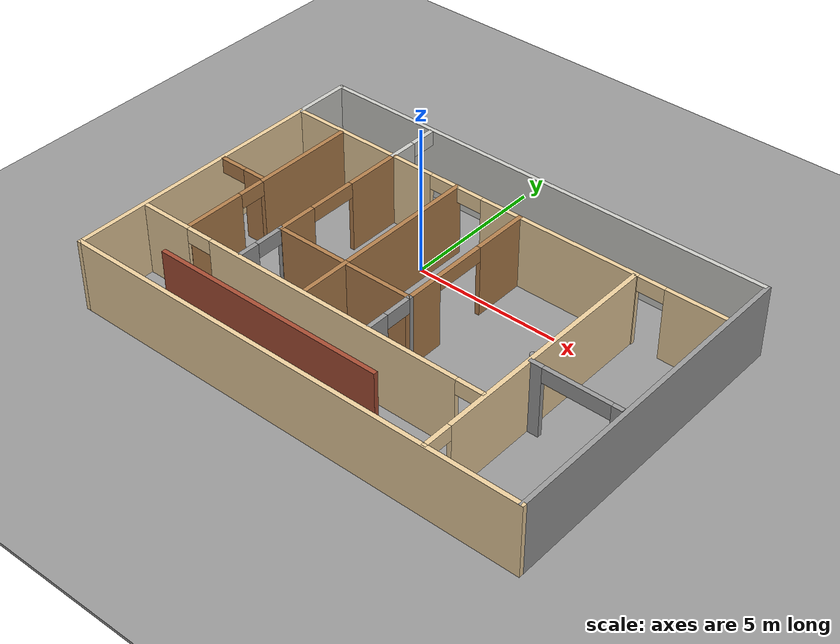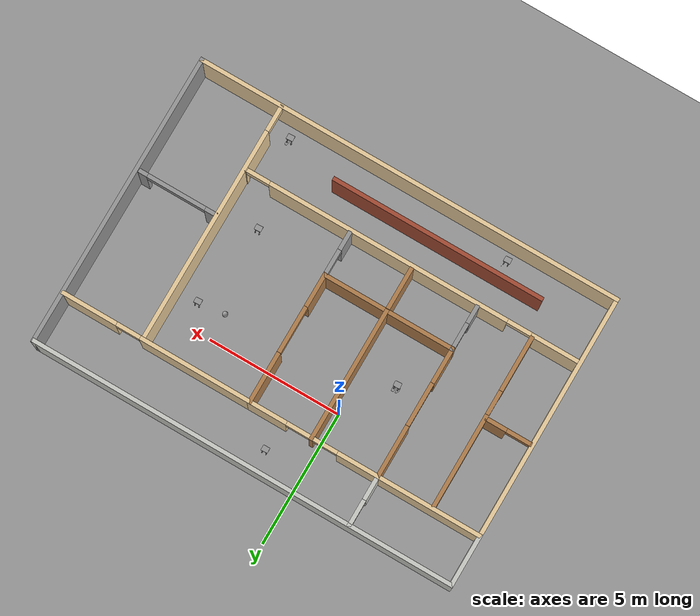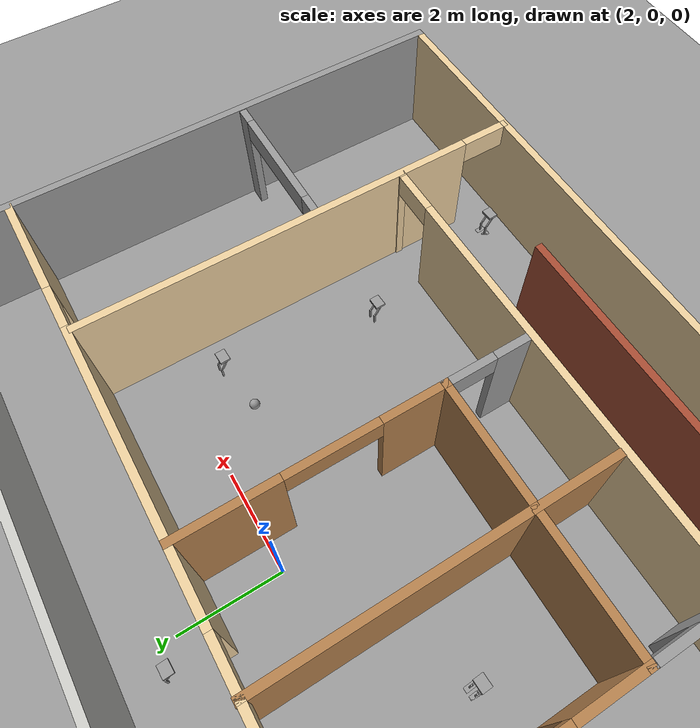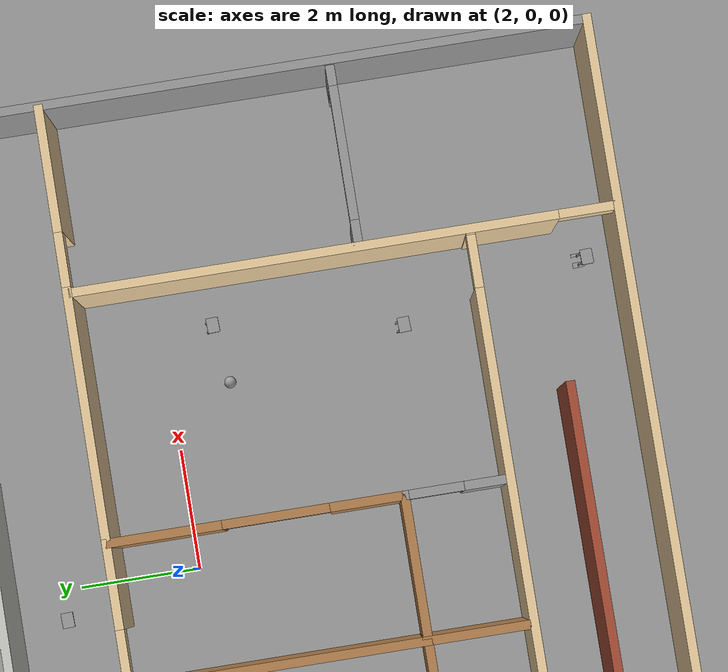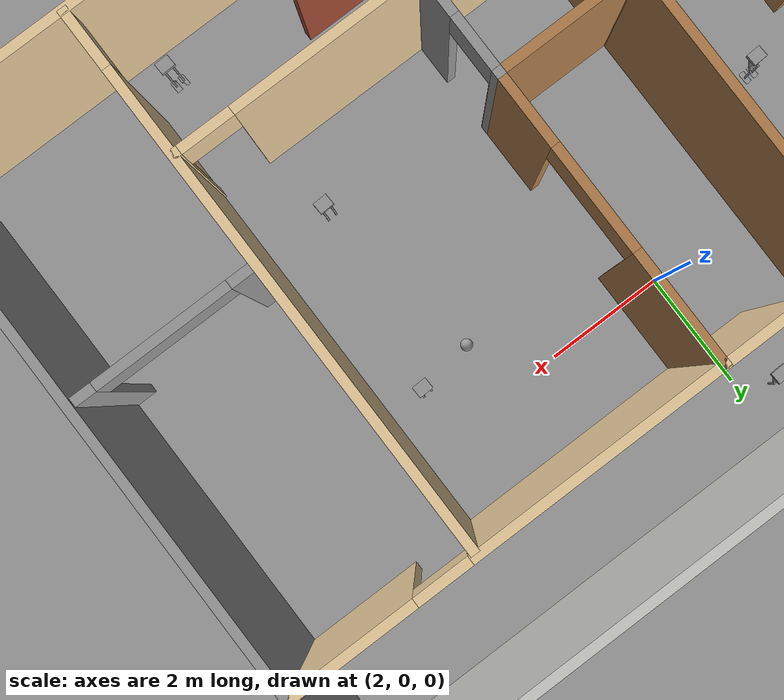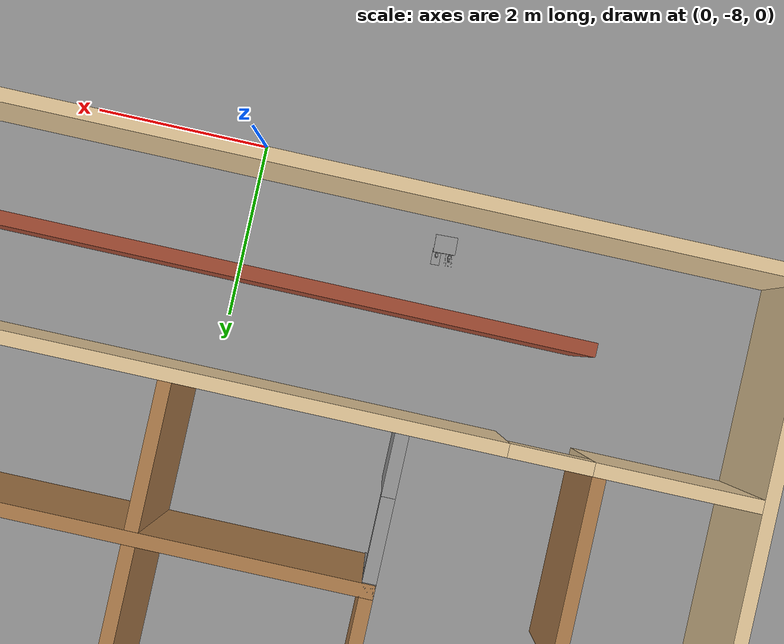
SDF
<sdf version="1.6">
 <world name="default">
  <plugin name="welcome_message" filename="libwelcome_message.so"/>
  <light name="sun" type="directional">
   <pose>0 0 10 0 -0 0</pose>
   <diffuse>0.8 0.8 0.8 1</diffuse>
   <specular>0.2 0.2 0.2 1</specular>
   <attenuation>
    <range>1000</range>
    <constant>0.9</constant>
    <linear>0.01</linear>
    <quadratic>0.001</quadratic>
   </attenuation>
   <direction>-0.5 0.1 -0.9</direction>
  </light>
  <model name="ground_plane">
   <static>1</static>
   <link name="link">
    <collision name="collision">
     <geometry><plane><normal>0 0 1</normal><size>100 100</size></plane></geometry>
     <surface><friction><ode><mu>100</mu><mu2>50</mu2></ode></friction></surface>
    </collision>
    <visual name="visual">
     <cast_shadows>0</cast_shadows>
     <geometry><plane><normal>0 0 1</normal><size>100 100</size></plane></geometry>
     <material>
      <script><uri>file://media/materials/scripts/gazebo.material</uri><name>Gazebo/Grey</name></script>
     </material>
    </visual>
   </link>
  </model>
  <gravity>0 0 -9.8</gravity>
  <magnetic_field>6e-06 2.3e-05 -4.2e-05</magnetic_field>
  <atmosphere type="adiabatic"/>
  <physics name="default_physics" default="0" type="ode">
   <max_step_size>0.001</max_step_size>
   <real_time_factor>1</real_time_factor>
   <real_time_update_rate>1000</real_time_update_rate>
  </physics>
  <scene><ambient>0.4 0.4 0.4 1</ambient><background>0.7 0.7 0.7 1</background><shadows>1</shadows></scene>
  <spherical_coordinates>
   <surface_model>EARTH_WGS84</surface_model>
   <latitude_deg>0</latitude_deg>
   <longitude_deg>0</longitude_deg>
   <elevation>0</elevation>
   <heading_deg>0</heading_deg>
  </spherical_coordinates>
  <model name="Building">
   <pose>1.84471 -2.27422 0 0 -0 0</pose>
   <link name="Wall_0">
    <collision name="Wall_0_Collision">
     <geometry><box><size>5 0.15 2.5</size></box></geometry>
     <pose>0 0 1.25 0 -0 0</pose>
    </collision>
    <visual name="Wall_0_Visual">
     <pose>0 0 1.25 0 -0 0</pose>
     <geometry><box><size>5 0.15 2.5</size></box></geometry>
     <material>
      <script><uri>file://media/materials/scripts/gazebo.material</uri><name>Gazebo/Wood</name></script>
      <ambient>1 1 1 1</ambient>
     </material>
     <meta><layer>0</layer></meta>
    </visual>
    <pose>-1.65 -1.275 0 0 -0 0</pose>
   </link>
   <link name="Wall_10">
    <collision name="Wall_10_Collision">
     <geometry><box><size>11 0.15 2.5</size></box></geometry>
     <pose>0 0 1.25 0 -0 0</pose>
    </collision>
    <visual name="Wall_10_Visual">
     <pose>0 0 1.25 0 -0 0</pose>
     <geometry><box><size>11 0.15 2.5</size></box></geometry>
     <material>
      <script><uri>file://media/materials/scripts/gazebo.material</uri><name>Gazebo/Grey</name></script>
      <ambient>1 1 1 1</ambient>
     </material>
     <meta><layer>0</layer></meta>
    </visual>
    <pose>7.925 0 0 0 0 -1.5708</pose>
   </link>
   <link name="Wall_11">
    <collision name="Wall_11_Collision">
     <geometry><box><size>16 0.15 2.5</size></box></geometry>
     <pose>0 0 1.25 0 -0 0</pose>
    </collision>
    <visual name="Wall_11_Visual">
     <pose>0 0 1.25 0 -0 0</pose>
     <geometry><box><size>16 0.15 2.5</size></box></geometry>
     <material>
      <script><uri>file://media/materials/scripts/gazebo.material</uri><name>Gazebo/Grey</name></script>
      <ambient>0.921569 0.807843 0.615686 1</ambient>
     </material>
     <meta><layer>0</layer></meta>
    </visual>
    <pose>0 -5.425 0 0 -0 3.14159</pose>
   </link>
   <link name="Wall_12">
    <collision name="Wall_12_Collision">
     <geometry><box><size>9.15 0.15 2.5</size></box></geometry>
     <pose>0 0 1.25 0 -0 0</pose>
    </collision>
    <visual name="Wall_12_Visual">
     <pose>0 0 1.25 0 -0 0</pose>
     <geometry><box><size>9.15 0.15 2.5</size></box></geometry>
     <material>
      <script><uri>file://media/materials/scripts/gazebo.material</uri><name>Gazebo/Grey</name></script>
      <ambient>0.921569 0.807843 0.615686 1</ambient>
     </material>
     <meta><layer>0</layer></meta>
    </visual>
    <pose>-7.925 -0.925 0 0 -0 1.5708</pose>
   </link>
   <link name="Wall_14">
    <collision name="Wall_14_Collision">
     <geometry><box><size>5 0.15 2.5</size></box></geometry>
     <pose>0 0 1.25 0 -0 0</pose>
    </collision>
    <visual name="Wall_14_Visual">
     <pose>0 0 1.25 0 -0 0</pose>
     <geometry><box><size>5 0.15 2.5</size></box></geometry>
     <material>
      <script><uri>file://media/materials/scripts/gazebo.material</uri><name>Gazebo/Wood</name></script>
      <ambient>1 1 1 1</ambient>
     </material>
     <meta><layer>0</layer></meta>
    </visual>
    <pose>-1.58093 1.16439 0 0 0 -1.5708</pose>
   </link>
   <link name="Wall_16">
    <pose>4.325 3.575 0 0 -0 0</pose>
    <visual name="Wall_16_Visual_0">
     <pose>-1.49954 0 1.25 0 -0 0</pose>
     <geometry><box><size>4.25093 0.15 2.5</size></box></geometry>
     <material>
      <script><uri>file://media/materials/scripts/gazebo.material</uri><name>Gazebo/Grey</name></script>
      <ambient>0.921569 0.807843 0.615686 1</ambient>
     </material>
     <meta><layer>0</layer></meta>
    </visual>
    <collision name="Wall_16_Collision_0">
     <geometry><box><size>4.25093 0.15 2.5</size></box></geometry>
     <pose>-1.49954 0 1.25 0 -0 0</pose>
    </collision>
    <visual name="Wall_16_Visual_1">
     <pose>2.57546 0 1.25 0 -0 0</pose>
     <geometry><box><size>2.09907 0.15 2.5</size></box></geometry>
     <material>
      <script><uri>file://media/materials/scripts/gazebo.material</uri><name>Gazebo/Grey</name></script>
      <ambient>0.921569 0.807843 0.615686 1</ambient>
     </material>
     <meta><layer>0</layer></meta>
    </visual>
    <collision name="Wall_16_Collision_1">
     <geometry><box><size>2.09907 0.15 2.5</size></box></geometry>
     <pose>2.57546 0 1.25 0 -0 0</pose>
    </collision>
    <visual name="Wall_16_Visual_2">
     <pose>1.07593 0 2.25 0 -0 0</pose>
     <geometry><box><size>0.9 0.15 0.5</size></box></geometry>
     <material>
      <script><uri>file://media/materials/scripts/gazebo.material</uri><name>Gazebo/Grey</name></script>
      <ambient>0.921569 0.807843 0.615686 1</ambient>
     </material>
     <meta><layer>0</layer></meta>
    </visual>
    <collision name="Wall_16_Collision_2">
     <geometry><box><size>0.9 0.15 0.5</size></box></geometry>
     <pose>1.07593 0 2.25 0 -0 0</pose>
    </collision>
   </link>
   <link name="Wall_2">
    <pose>-4.075 1.15 0 0 -0 1.5708</pose>
    <visual name="Wall_2_Visual_0">
     <pose>-1.81088 0 1.25 0 -0 0</pose>
     <geometry><box><size>1.37824 0.15 2.5</size></box></geometry>
     <material>
      <script><uri>file://media/materials/scripts/gazebo.material</uri><name>Gazebo/Wood</name></script>
      <ambient>1 1 1 1</ambient>
     </material>
     <meta><layer>0</layer></meta>
    </visual>
    <collision name="Wall_2_Collision_0">
     <geometry><box><size>1.37824 0.15 2.5</size></box></geometry>
     <pose>-1.81088 0 1.25 0 -0 0</pose>
    </collision>
    <visual name="Wall_2_Visual_1">
     <pose>1.50207 0 1.25 0 -0 0</pose>
     <geometry><box><size>1.99587 0.15 2.5</size></box></geometry>
     <material>
      <script><uri>file://media/materials/scripts/gazebo.material</uri><name>Gazebo/Wood</name></script>
      <ambient>1 1 1 1</ambient>
     </material>
     <meta><layer>0</layer></meta>
    </visual>
    <collision name="Wall_2_Collision_1">
     <geometry><box><size>1.99587 0.15 2.5</size></box></geometry>
     <pose>1.50207 0 1.25 0 -0 0</pose>
    </collision>
    <visual name="Wall_2_Visual_2">
     <pose>-0.308816 0 2.25 0 -0 0</pose>
     <geometry><box><size>1.6259 0.15 0.5</size></box></geometry>
     <material>
      <script><uri>file://media/materials/scripts/gazebo.material</uri><name>Gazebo/Wood</name></script>
      <ambient>1 1 1 1</ambient>
     </material>
     <meta><layer>0</layer></meta>
    </visual>
    <collision name="Wall_2_Collision_2">
     <geometry><box><size>1.6259 0.15 0.5</size></box></geometry>
     <pose>-0.308816 0 2.25 0 -0 0</pose>
    </collision>
   </link>
   <link name="Wall_22">
    <pose>4.85192 -0.951678 0 0 0 -1.5708</pose>
    <visual name="Wall_22_Visual_0">
     <pose>-0.499013 0 1.25 0 -0 0</pose>
     <geometry><box><size>8.00197 0.15 2.5</size></box></geometry>
     <material>
      <script><uri>file://media/materials/scripts/gazebo.material</uri><name>Gazebo/Grey</name></script>
      <ambient>0.921569 0.807843 0.615686 1</ambient>
     </material>
     <meta><layer>0</layer></meta>
    </visual>
    <collision name="Wall_22_Collision_0">
     <geometry><box><size>8.00197 0.15 2.5</size></box></geometry>
     <pose>-0.499013 0 1.25 0 -0 0</pose>
    </collision>
    <visual name="Wall_22_Visual_1">
     <pose>4.45099 0 1.25 0 -0 0</pose>
     <geometry><box><size>0.098027 0.15 2.5</size></box></geometry>
     <material>
      <script><uri>file://media/materials/scripts/gazebo.material</uri><name>Gazebo/Grey</name></script>
      <ambient>0.921569 0.807843 0.615686 1</ambient>
     </material>
     <meta><layer>0</layer></meta>
    </visual>
    <collision name="Wall_22_Collision_1">
     <geometry><box><size>0.098027 0.15 2.5</size></box></geometry>
     <pose>4.45099 0 1.25 0 -0 0</pose>
    </collision>
    <visual name="Wall_22_Visual_2">
     <pose>3.95197 0 2.25 0 -0 0</pose>
     <geometry><box><size>0.9 0.15 0.5</size></box></geometry>
     <material>
      <script><uri>file://media/materials/scripts/gazebo.material</uri><name>Gazebo/Grey</name></script>
      <ambient>0.921569 0.807843 0.615686 1</ambient>
     </material>
     <meta><layer>0</layer></meta>
    </visual>
    <collision name="Wall_22_Collision_2">
     <geometry><box><size>0.9 0.15 0.5</size></box></geometry>
     <pose>3.95197 0 2.25 0 -0 0</pose>
    </collision>
   </link>
   <link name="Wall_25">
    <pose>-1.48306 -2.998 0 0 -0 3.14159</pose>
    <visual name="Wall_25_Visual_0">
     <pose>-6.30396 0 1.25 0 -0 0</pose>
     <geometry><box><size>0.142088 0.15 2.5</size></box></geometry>
     <material>
      <script><uri>file://media/materials/scripts/gazebo.material</uri><name>Gazebo/Grey</name></script>
      <ambient>0.921569 0.807843 0.615686 1</ambient>
     </material>
     <meta><layer>0</layer></meta>
    </visual>
    <collision name="Wall_25_Collision_0">
     <geometry><box><size>0.142088 0.15 2.5</size></box></geometry>
     <pose>-6.30396 0 1.25 0 -0 0</pose>
    </collision>
    <visual name="Wall_25_Visual_1">
     <pose>-0.838657 0 1.25 0 -0 0</pose>
     <geometry><box><size>9.05712 0.15 2.5</size></box></geometry>
     <material>
      <script><uri>file://media/materials/scripts/gazebo.material</uri><name>Gazebo/Grey</name></script>
      <ambient>0.921569 0.807843 0.615686 1</ambient>
     </material>
     <meta><layer>0</layer></meta>
    </visual>
    <collision name="Wall_25_Collision_1">
     <geometry><box><size>9.05712 0.15 2.5</size></box></geometry>
     <pose>-0.838657 0 1.25 0 -0 0</pose>
    </collision>
    <visual name="Wall_25_Visual_2">
     <pose>5.48245 0 1.25 0 -0 0</pose>
     <geometry><box><size>1.7851 0.15 2.5</size></box></geometry>
     <material>
      <script><uri>file://media/materials/scripts/gazebo.material</uri><name>Gazebo/Grey</name></script>
      <ambient>0.921569 0.807843 0.615686 1</ambient>
     </material>
     <meta><layer>0</layer></meta>
    </visual>
    <collision name="Wall_25_Collision_2">
     <geometry><box><size>1.7851 0.15 2.5</size></box></geometry>
     <pose>5.48245 0 1.25 0 -0 0</pose>
    </collision>
    <visual name="Wall_25_Visual_3">
     <pose>-5.80007 0 2.25 0 -0 0</pose>
     <geometry><box><size>0.865695 0.15 0.5</size></box></geometry>
     <material>
      <script><uri>file://media/materials/scripts/gazebo.material</uri><name>Gazebo/Grey</name></script>
      <ambient>0.921569 0.807843 0.615686 1</ambient>
     </material>
     <meta><layer>0</layer></meta>
    </visual>
    <collision name="Wall_25_Collision_3">
     <geometry><box><size>0.865695 0.15 0.5</size></box></geometry>
     <pose>-5.80007 0 2.25 0 -0 0</pose>
    </collision>
    <visual name="Wall_25_Visual_4">
     <pose>4.1399 0 2.25 0 -0 0</pose>
     <geometry><box><size>0.9 0.15 0.5</size></box></geometry>
     <material>
      <script><uri>file://media/materials/scripts/gazebo.material</uri><name>Gazebo/Grey</name></script>
      <ambient>0.921569 0.807843 0.615686 1</ambient>
     </material>
     <meta><layer>0</layer></meta>
    </visual>
    <collision name="Wall_25_Collision_4">
     <geometry><box><size>0.9 0.15 0.5</size></box></geometry>
     <pose>4.1399 0 2.25 0 -0 0</pose>
    </collision>
   </link>
   <link name="Wall_27">
    <pose>-6.14068 0.284689 0 0 0 -1.5708</pose>
    <visual name="Wall_27_Visual_0">
     <pose>-1.49304 0 1.25 0 -0 0</pose>
     <geometry><box><size>3.51392 0.15 2.5</size></box></geometry>
     <material>
      <script><uri>file://media/materials/scripts/gazebo.material</uri><name>Gazebo/Wood</name></script>
      <ambient>1 1 1 1</ambient>
     </material>
     <meta><layer>0</layer></meta>
    </visual>
    <collision name="Wall_27_Collision_0">
     <geometry><box><size>3.51392 0.15 2.5</size></box></geometry>
     <pose>-1.49304 0 1.25 0 -0 0</pose>
    </collision>
    <visual name="Wall_27_Visual_1">
     <pose>2.20696 0 1.25 0 -0 0</pose>
     <geometry><box><size>2.08608 0.15 2.5</size></box></geometry>
     <material>
      <script><uri>file://media/materials/scripts/gazebo.material</uri><name>Gazebo/Wood</name></script>
      <ambient>1 1 1 1</ambient>
     </material>
     <meta><layer>0</layer></meta>
    </visual>
    <collision name="Wall_27_Collision_1">
     <geometry><box><size>2.08608 0.15 2.5</size></box></geometry>
     <pose>2.20696 0 1.25 0 -0 0</pose>
    </collision>
    <visual name="Wall_27_Visual_2">
     <pose>0.713923 0 2.25 0 -0 0</pose>
     <geometry><box><size>0.9 0.15 0.5</size></box></geometry>
     <material>
      <script><uri>file://media/materials/scripts/gazebo.material</uri><name>Gazebo/Wood</name></script>
      <ambient>1 1 1 1</ambient>
     </material>
     <meta><layer>0</layer></meta>
    </visual>
    <collision name="Wall_27_Collision_2">
     <geometry><box><size>0.9 0.15 0.5</size></box></geometry>
     <pose>0.713923 0 2.25 0 -0 0</pose>
    </collision>
   </link>
   <link name="Wall_29">
    <pose>6.3362 -1.18544 0 0 -0 0</pose>
    <visual name="Wall_29_Visual_0">
     <pose>-1.27306 0 1.25 0 -0 0</pose>
     <geometry><box><size>0.453869 0.15 2.5</size></box></geometry>
     <material>
      <script><uri>file://media/materials/scripts/gazebo.material</uri><name>Gazebo/Grey</name></script>
      <ambient>1 1 1 1</ambient>
     </material>
     <meta><layer>0</layer></meta>
    </visual>
    <collision name="Wall_29_Collision_0">
     <geometry><box><size>0.453869 0.15 2.5</size></box></geometry>
     <pose>-1.27306 0 1.25 0 -0 0</pose>
    </collision>
    <visual name="Wall_29_Visual_1">
     <pose>1.33007 0 1.25 0 -0 0</pose>
     <geometry><box><size>0.339865 0.15 2.5</size></box></geometry>
     <material>
      <script><uri>file://media/materials/scripts/gazebo.material</uri><name>Gazebo/Grey</name></script>
      <ambient>1 1 1 1</ambient>
     </material>
     <meta><layer>0</layer></meta>
    </visual>
    <collision name="Wall_29_Collision_1">
     <geometry><box><size>0.339865 0.15 2.5</size></box></geometry>
     <pose>1.33007 0 1.25 0 -0 0</pose>
    </collision>
    <visual name="Wall_29_Visual_2">
     <pose>0.057002 0 2.25 0 -0 0</pose>
     <geometry><box><size>2.20627 0.15 0.5</size></box></geometry>
     <material>
      <script><uri>file://media/materials/scripts/gazebo.material</uri><name>Gazebo/Grey</name></script>
      <ambient>1 1 1 1</ambient>
     </material>
     <meta><layer>0</layer></meta>
    </visual>
    <collision name="Wall_29_Collision_2">
     <geometry><box><size>2.20627 0.15 0.5</size></box></geometry>
     <pose>0.057002 0 2.25 0 -0 0</pose>
    </collision>
   </link>
   <link name="Wall_3">
    <pose>-1.65 3.575 0 0 -0 0</pose>
    <visual name="Wall_3_Visual_0">
     <pose>-1.69786 0 1.25 0 -0 0</pose>
     <geometry><box><size>1.60428 0.15 2.5</size></box></geometry>
     <material>
      <script><uri>file://media/materials/scripts/gazebo.material</uri><name>Gazebo/Grey</name></script>
      <ambient>0.921569 0.807843 0.615686 1</ambient>
     </material>
     <meta><layer>0</layer></meta>
    </visual>
    <collision name="Wall_3_Collision_0">
     <geometry><box><size>1.60428 0.15 2.5</size></box></geometry>
     <pose>-1.69786 0 1.25 0 -0 0</pose>
    </collision>
    <visual name="Wall_3_Visual_1">
     <pose>0.066943 0 1.25 0 -0 0</pose>
     <geometry><box><size>0.125322 0.15 2.5</size></box></geometry>
     <material>
      <script><uri>file://media/materials/scripts/gazebo.material</uri><name>Gazebo/Grey</name></script>
      <ambient>0.921569 0.807843 0.615686 1</ambient>
     </material>
     <meta><layer>0</layer></meta>
    </visual>
    <collision name="Wall_3_Collision_1">
     <geometry><box><size>0.125322 0.15 2.5</size></box></geometry>
     <pose>0.066943 0 1.25 0 -0 0</pose>
    </collision>
    <visual name="Wall_3_Visual_2">
     <pose>1.7648 0 1.25 0 -0 0</pose>
     <geometry><box><size>1.4704 0.15 2.5</size></box></geometry>
     <material>
      <script><uri>file://media/materials/scripts/gazebo.material</uri><name>Gazebo/Grey</name></script>
      <ambient>0.921569 0.807843 0.615686 1</ambient>
     </material>
     <meta><layer>0</layer></meta>
    </visual>
    <collision name="Wall_3_Collision_2">
     <geometry><box><size>1.4704 0.15 2.5</size></box></geometry>
     <pose>1.7648 0 1.25 0 -0 0</pose>
    </collision>
    <visual name="Wall_3_Visual_3">
     <pose>-0.445718 0 2.25 0 -0 0</pose>
     <geometry><box><size>0.9 0.15 0.5</size></box></geometry>
     <material>
      <script><uri>file://media/materials/scripts/gazebo.material</uri><name>Gazebo/Grey</name></script>
      <ambient>0.921569 0.807843 0.615686 1</ambient>
     </material>
     <meta><layer>0</layer></meta>
    </visual>
    <collision name="Wall_3_Collision_3">
     <geometry><box><size>0.9 0.15 0.5</size></box></geometry>
     <pose>-0.445718 0 2.25 0 -0 0</pose>
    </collision>
    <visual name="Wall_3_Visual_4">
     <pose>0.579604 0 2.25 0 -0 0</pose>
     <geometry><box><size>0.9 0.15 0.5</size></box></geometry>
     <material>
      <script><uri>file://media/materials/scripts/gazebo.material</uri><name>Gazebo/Grey</name></script>
      <ambient>0.921569 0.807843 0.615686 1</ambient>
     </material>
     <meta><layer>0</layer></meta>
    </visual>
    <collision name="Wall_3_Collision_4">
     <geometry><box><size>0.9 0.15 0.5</size></box></geometry>
     <pose>0.579604 0 2.25 0 -0 0</pose>
    </collision>
   </link>
   <link name="Wall_31">
    <pose>-7.02156 0.143806 0 0 -0 0</pose>
    <visual name="Wall_31_Visual_0">
     <pose>-0.852619 0 1.25 0 -0 0</pose>
     <geometry><box><size>0.044761 0.15 2.5</size></box></geometry>
     <material>
      <script><uri>file://media/materials/scripts/gazebo.material</uri><name>Gazebo/Wood</name></script>
      <ambient>1 1 1 1</ambient>
     </material>
     <meta><layer>0</layer></meta>
    </visual>
    <collision name="Wall_31_Collision_0">
     <geometry><box><size>0.044761 0.15 2.5</size></box></geometry>
     <pose>-0.852619 0 1.25 0 -0 0</pose>
    </collision>
    <visual name="Wall_31_Visual_1">
     <pose>0.472381 0 1.25 0 -0 0</pose>
     <geometry><box><size>0.805239 0.15 2.5</size></box></geometry>
     <material>
      <script><uri>file://media/materials/scripts/gazebo.material</uri><name>Gazebo/Wood</name></script>
      <ambient>1 1 1 1</ambient>
     </material>
     <meta><layer>0</layer></meta>
    </visual>
    <collision name="Wall_31_Collision_1">
     <geometry><box><size>0.805239 0.15 2.5</size></box></geometry>
     <pose>0.472381 0 1.25 0 -0 0</pose>
    </collision>
    <visual name="Wall_31_Visual_2">
     <pose>-0.380239 0 2.25 0 -0 0</pose>
     <geometry><box><size>0.9 0.15 0.5</size></box></geometry>
     <material>
      <script><uri>file://media/materials/scripts/gazebo.material</uri><name>Gazebo/Wood</name></script>
      <ambient>1 1 1 1</ambient>
     </material>
     <meta><layer>0</layer></meta>
    </visual>
    <collision name="Wall_31_Collision_2">
     <geometry><box><size>0.9 0.15 0.5</size></box></geometry>
     <pose>-0.380239 0 2.25 0 -0 0</pose>
    </collision>
   </link>
   <link name="Wall_33">
    <collision name="Wall_33_Collision">
     <geometry><box><size>8 0.15 2.5</size></box></geometry>
     <pose>0 0 1.25 0 -0 0</pose>
    </collision>
    <visual name="Wall_33_Visual">
     <pose>0 0 1.25 0 -0 0</pose>
     <geometry><box><size>8 0.15 2.5</size></box></geometry>
     <material>
      <script><uri>file://media/materials/scripts/gazebo.material</uri><name>Gazebo/Bricks</name></script>
      <ambient>1 1 1 1</ambient>
     </material>
     <meta><layer>0</layer></meta>
    </visual>
    <pose>-1.83273 -4.19373 0 0 -0 0</pose>
   </link>
   <link name="Wall_35">
    <collision name="Wall_35_Collision">
     <geometry><box><size>1.75 0.15 2.5</size></box></geometry>
     <pose>0 0 1.25 0 -0 0</pose>
    </collision>
    <visual name="Wall_35_Visual">
     <pose>0 0 1.25 0 -0 0</pose>
     <geometry><box><size>1.75 0.15 2.5</size></box></geometry>
     <material>
      <script><uri>file://media/materials/scripts/gazebo.material</uri><name>Gazebo/Wood</name></script>
      <ambient>0.435294 0.796078 0.67451 1</ambient>
     </material>
     <meta><layer>0</layer></meta>
    </visual>
    <pose>-1.58093 -2.06061 0 0 0 -1.5708</pose>
   </link>
   <link name="Wall_37">
    <pose>-4.075 -2.075 0 0 0 -1.5708</pose>
    <visual name="Wall_37_Visual_0">
     <pose>-0.795598 0 1.25 0 -0 0</pose>
     <geometry><box><size>0.158804 0.15 2.5</size></box></geometry>
     <material>
      <script><uri>file://media/materials/scripts/gazebo.material</uri><name>Gazebo/Grey</name></script>
      <ambient>1 1 1 1</ambient>
     </material>
     <meta><layer>0</layer></meta>
    </visual>
    <collision name="Wall_37_Collision_0">
     <geometry><box><size>0.158804 0.15 2.5</size></box></geometry>
     <pose>-0.795598 0 1.25 0 -0 0</pose>
    </collision>
    <visual name="Wall_37_Visual_1">
     <pose>0.529402 0 1.25 0 -0 0</pose>
     <geometry><box><size>0.691196 0.15 2.5</size></box></geometry>
     <material>
      <script><uri>file://media/materials/scripts/gazebo.material</uri><name>Gazebo/Grey</name></script>
      <ambient>1 1 1 1</ambient>
     </material>
     <meta><layer>0</layer></meta>
    </visual>
    <collision name="Wall_37_Collision_1">
     <geometry><box><size>0.691196 0.15 2.5</size></box></geometry>
     <pose>0.529402 0 1.25 0 -0 0</pose>
    </collision>
    <visual name="Wall_37_Visual_2">
     <pose>-0.266196 0 2.25 0 -0 0</pose>
     <geometry><box><size>0.9 0.15 0.5</size></box></geometry>
     <material>
      <script><uri>file://media/materials/scripts/gazebo.material</uri><name>Gazebo/Grey</name></script>
      <ambient>1 1 1 1</ambient>
     </material>
     <meta><layer>0</layer></meta>
    </visual>
    <collision name="Wall_37_Collision_2">
     <geometry><box><size>0.9 0.15 0.5</size></box></geometry>
     <pose>-0.266196 0 2.25 0 -0 0</pose>
    </collision>
   </link>
   <link name="Wall_39">
    <pose>0.775 -2.075 0 0 0 -1.5708</pose>
    <visual name="Wall_39_Visual_0">
     <pose>-0.804422 0 1.25 0 -0 0</pose>
     <geometry><box><size>0.141156 0.15 2.5</size></box></geometry>
     <material>
      <script><uri>file://media/materials/scripts/gazebo.material</uri><name>Gazebo/Grey</name></script>
      <ambient>1 1 1 1</ambient>
     </material>
     <meta><layer>0</layer></meta>
    </visual>
    <collision name="Wall_39_Collision_0">
     <geometry><box><size>0.141156 0.15 2.5</size></box></geometry>
     <pose>-0.804422 0 1.25 0 -0 0</pose>
    </collision>
    <visual name="Wall_39_Visual_1">
     <pose>0.520578 0 1.25 0 -0 0</pose>
     <geometry><box><size>0.708844 0.15 2.5</size></box></geometry>
     <material>
      <script><uri>file://media/materials/scripts/gazebo.material</uri><name>Gazebo/Grey</name></script>
      <ambient>1 1 1 1</ambient>
     </material>
     <meta><layer>0</layer></meta>
    </visual>
    <collision name="Wall_39_Collision_1">
     <geometry><box><size>0.708844 0.15 2.5</size></box></geometry>
     <pose>0.520578 0 1.25 0 -0 0</pose>
    </collision>
    <visual name="Wall_39_Visual_2">
     <pose>-0.283844 0 2.25 0 -0 0</pose>
     <geometry><box><size>0.9 0.15 0.5</size></box></geometry>
     <material>
      <script><uri>file://media/materials/scripts/gazebo.material</uri><name>Gazebo/Grey</name></script>
      <ambient>1 1 1 1</ambient>
     </material>
     <meta><layer>0</layer></meta>
    </visual>
    <collision name="Wall_39_Collision_2">
     <geometry><box><size>0.9 0.15 0.5</size></box></geometry>
     <pose>-0.283844 0 2.25 0 -0 0</pose>
    </collision>
   </link>
   <link name="Wall_4">
    <pose>0.775 1.15 0 0 0 -1.5708</pose>
    <visual name="Wall_4_Visual_0">
     <pose>-1.52402 0 1.25 0 -0 0</pose>
     <geometry><box><size>1.95195 0.15 2.5</size></box></geometry>
     <material>
      <script><uri>file://media/materials/scripts/gazebo.material</uri><name>Gazebo/Wood</name></script>
      <ambient>1 1 1 1</ambient>
     </material>
     <meta><layer>0</layer></meta>
    </visual>
    <collision name="Wall_4_Collision_0">
     <geometry><box><size>1.95195 0.15 2.5</size></box></geometry>
     <pose>-1.52402 0 1.25 0 -0 0</pose>
    </collision>
    <visual name="Wall_4_Visual_1">
     <pose>1.85273 0 1.25 0 -0 0</pose>
     <geometry><box><size>1.29455 0.15 2.5</size></box></geometry>
     <material>
      <script><uri>file://media/materials/scripts/gazebo.material</uri><name>Gazebo/Wood</name></script>
      <ambient>1 1 1 1</ambient>
     </material>
     <meta><layer>0</layer></meta>
    </visual>
    <collision name="Wall_4_Collision_1">
     <geometry><box><size>1.29455 0.15 2.5</size></box></geometry>
     <pose>1.85273 0 1.25 0 -0 0</pose>
    </collision>
    <visual name="Wall_4_Visual_2">
     <pose>0.328703 0 2.25 0 -0 0</pose>
     <geometry><box><size>1.7535 0.15 0.5</size></box></geometry>
     <material>
      <script><uri>file://media/materials/scripts/gazebo.material</uri><name>Gazebo/Wood</name></script>
      <ambient>1 1 1 1</ambient>
     </material>
     <meta><layer>0</layer></meta>
    </visual>
    <collision name="Wall_4_Collision_2">
     <geometry><box><size>1.7535 0.15 0.5</size></box></geometry>
     <pose>0.328703 0 2.25 0 -0 0</pose>
    </collision>
   </link>
   <link name="Wall_42">
    <pose>-4.075 4.5 0 0 -0 1.5708</pose>
    <visual name="Wall_42_Visual_0">
     <pose>-0.518886 0 1.25 0 -0 0</pose>
     <geometry><box><size>0.962229 0.15 2.5</size></box></geometry>
     <material>
      <script><uri>file://media/materials/scripts/gazebo.material</uri><name>Gazebo/CeilingTiled</name></script>
      <ambient>1 1 1 1</ambient>
     </material>
     <meta><layer>0</layer></meta>
    </visual>
    <collision name="Wall_42_Collision_0">
     <geometry><box><size>0.962229 0.15 2.5</size></box></geometry>
     <pose>-0.518886 0 1.25 0 -0 0</pose>
    </collision>
    <visual name="Wall_42_Visual_1">
     <pose>0.931114 0 1.25 0 -0 0</pose>
     <geometry><box><size>0.137771 0.15 2.5</size></box></geometry>
     <material>
      <script><uri>file://media/materials/scripts/gazebo.material</uri><name>Gazebo/CeilingTiled</name></script>
      <ambient>1 1 1 1</ambient>
     </material>
     <meta><layer>0</layer></meta>
    </visual>
    <collision name="Wall_42_Collision_1">
     <geometry><box><size>0.137771 0.15 2.5</size></box></geometry>
     <pose>0.931114 0 1.25 0 -0 0</pose>
    </collision>
    <visual name="Wall_42_Visual_2">
     <pose>0.412229 0 2.25 0 -0 0</pose>
     <geometry><box><size>0.9 0.15 0.5</size></box></geometry>
     <material>
      <script><uri>file://media/materials/scripts/gazebo.material</uri><name>Gazebo/CeilingTiled</name></script>
      <ambient>1 1 1 1</ambient>
     </material>
     <meta><layer>0</layer></meta>
    </visual>
    <collision name="Wall_42_Collision_2">
     <geometry><box><size>0.9 0.15 0.5</size></box></geometry>
     <pose>0.412229 0 2.25 0 -0 0</pose>
    </collision>
   </link>
   <link name="Wall_6">
    <collision name="Wall_6_Collision">
     <geometry><box><size>4 0.15 2.5</size></box></geometry>
     <pose>0 0 1.25 0 -0 0</pose>
    </collision>
    <visual name="Wall_6_Visual">
     <pose>0 0 1.25 0 -0 0</pose>
     <geometry><box><size>4 0.15 2.5</size></box></geometry>
     <material>
      <script><uri>file://media/materials/scripts/gazebo.material</uri><name>Gazebo/Grey</name></script>
      <ambient>0.921569 0.807843 0.615686 1</ambient>
     </material>
     <meta><layer>0</layer></meta>
    </visual>
    <pose>-6 3.575 0 0 -0 3.14159</pose>
   </link>
   <link name="Wall_7">
    <collision name="Wall_7_Collision">
     <geometry><box><size>2 0.15 2.5</size></box></geometry>
     <pose>0 0 1.25 0 -0 0</pose>
    </collision>
    <visual name="Wall_7_Visual">
     <pose>0 0 1.25 0 -0 0</pose>
     <geometry><box><size>2 0.15 2.5</size></box></geometry>
     <material>
      <script><uri>file://media/materials/scripts/gazebo.material</uri><name>Gazebo/CeilingTiled</name></script>
      <ambient>1 1 1 1</ambient>
     </material>
     <meta><layer>0</layer></meta>
    </visual>
    <pose>-7.925 4.5 0 0 -0 1.5708</pose>
   </link>
   <link name="Wall_9">
    <collision name="Wall_9_Collision">
     <geometry><box><size>16 0.15 2.5</size></box></geometry>
     <pose>0 0 1.25 0 -0 0</pose>
    </collision>
    <visual name="Wall_9_Visual">
     <pose>0 0 1.25 0 -0 0</pose>
     <geometry><box><size>16 0.15 2.5</size></box></geometry>
     <material>
      <script><uri>file://media/materials/scripts/gazebo.material</uri><name>Gazebo/CeilingTiled</name></script>
      <ambient>1 1 1 1</ambient>
     </material>
     <meta><layer>0</layer></meta>
    </visual>
    <pose>0 5.425 0 0 -0 0</pose>
   </link>
   <static>1</static>
  </model>
  <model name="ground_plane_0">
   <static>1</static>
   <link name="link">
    <collision name="collision">
     <geometry><plane><normal>0 0 1</normal><size>100 100</size></plane></geometry>
     <surface><friction><ode><mu>100</mu><mu2>50</mu2></ode></friction></surface>
    </collision>
    <visual name="visual">
     <cast_shadows>0</cast_shadows>
     <geometry><plane><normal>0 0 1</normal><size>100 100</size></plane></geometry>
     <material>
      <script><uri>file://media/materials/scripts/gazebo.material</uri><name>Gazebo/Grey</name></script>
     </material>
    </visual>
   </link>
   <pose>4.39275 -1.64817 0 0 -0 0</pose>
  </model>
  <model name="HumonoidRobot">
   <link name="link_0">
    <pose>-0.075081 0.045022 -0.236474 0 -0 0</pose>
    <inertial>
     <mass>1</mass>
     <inertia>
      <ixx>0.166667</ixx>
      <ixy>0</ixy>
      <ixz>0</ixz>
      <iyy>0.166667</iyy>
      <iyz>0</iyz>
      <izz>0.166667</izz>
     </inertia>
    </inertial>
    <visual name="visual">
     <geometry><box><size>0.1 0.2 0.05</size></box></geometry>
     <material>
      <lighting>1</lighting>
      <script><uri>file://media/materials/scripts/gazebo.material</uri><name>Gazebo/Grey</name></script>
      <shader type="pixel"><normal_map>__default__</normal_map></shader>
      <ambient>0.3 0.3 0.3 1</ambient>
      <diffuse>0.7 0.7 0.7 1</diffuse>
      <specular>0.01 0.01 0.01 1</specular>
      <emissive>0 0 0 1</emissive>
     </material>
    </visual>
    <collision name="collision">
     <geometry><box><size>0.1 0.2 0.05</size></box></geometry>
     <surface>
      <friction>
       <ode><mu>1</mu><mu2>1</mu2><fdir1>0 0 0</fdir1><slip1>0</slip1><slip2>0</slip2></ode>
       <torsional>
        <coefficient>1</coefficient>
        <patch_radius>0</patch_radius>
        <surface_radius>0</surface_radius>
        <use_patch_radius>1</use_patch_radius>
        <ode><slip>0</slip></ode>
       </torsional>
      </friction>
      <bounce><restitution_coefficient>0</restitution_coefficient><threshold>1e+06</threshold></bounce>
      <contact>
       <collide_without_contact>0</collide_without_contact>
       <collide_without_contact_bitmask>1</collide_without_contact_bitmask>
       <collide_bitmask>1</collide_bitmask>
       <ode>
        <soft_cfm>0</soft_cfm>
        <soft_erp>0.2</soft_erp>
        <kp>1e+13</kp>
        <kd>1</kd>
        <max_vel>0.01</max_vel>
        <min_depth>0</min_depth>
       </ode>
       <bullet>
        <split_impulse>1</split_impulse>
        <split_impulse_penetration_threshold>-0.01</split_impulse_penetration_threshold>
        <soft_cfm>0</soft_cfm>
        <soft_erp>0.2</soft_erp>
        <kp>1e+13</kp>
        <kd>1</kd>
       </bullet>
      </contact>
     </surface>
    </collision>
   </link>
   <link name="link_0_clone">
    <pose>0.074919 0.045022 -0.236474 0 -0 0</pose>
    <inertial>
     <mass>1</mass>
     <inertia>
      <ixx>0.166667</ixx>
      <ixy>0</ixy>
      <ixz>0</ixz>
      <iyy>0.166667</iyy>
      <iyz>0</iyz>
      <izz>0.166667</izz>
     </inertia>
    </inertial>
    <visual name="visual">
     <geometry><box><size>0.1 0.2 0.05</size></box></geometry>
     <material>
      <lighting>1</lighting>
      <script><uri>file://media/materials/scripts/gazebo.material</uri><name>Gazebo/Grey</name></script>
      <shader type="pixel"><normal_map>__default__</normal_map></shader>
      <ambient>0.3 0.3 0.3 1</ambient>
      <diffuse>0.7 0.7 0.7 1</diffuse>
      <specular>0.01 0.01 0.01 1</specular>
      <emissive>0 0 0 1</emissive>
     </material>
    </visual>
    <collision name="collision">
     <geometry><box><size>0.1 0.2 0.05</size></box></geometry>
     <surface>
      <friction>
       <ode><mu>1</mu><mu2>1</mu2><fdir1>0 0 0</fdir1><slip1>0</slip1><slip2>0</slip2></ode>
       <torsional>
        <coefficient>1</coefficient>
        <patch_radius>0</patch_radius>
        <surface_radius>0</surface_radius>
        <use_patch_radius>1</use_patch_radius>
        <ode><slip>0</slip></ode>
       </torsional>
      </friction>
      <bounce><restitution_coefficient>0</restitution_coefficient><threshold>1e+06</threshold></bounce>
      <contact>
       <collide_without_contact>0</collide_without_contact>
       <collide_without_contact_bitmask>1</collide_without_contact_bitmask>
       <collide_bitmask>1</collide_bitmask>
       <ode>
        <soft_cfm>0</soft_cfm>
        <soft_erp>0.2</soft_erp>
        <kp>1e+13</kp>
        <kd>1</kd>
        <max_vel>0.01</max_vel>
        <min_depth>0</min_depth>
       </ode>
       <bullet>
        <split_impulse>1</split_impulse>
        <split_impulse_penetration_threshold>-0.01</split_impulse_penetration_threshold>
        <soft_cfm>0</soft_cfm>
        <soft_erp>0.2</soft_erp>
        <kp>1e+13</kp>
        <kd>1</kd>
       </bullet>
      </contact>
     </surface>
    </collision>
   </link>
   <link name="link_0_clone_0">
    <pose>0.000486 -0.069978 0.341184 0 -0 0</pose>
    <inertial>
     <mass>1</mass>
     <inertia>
      <ixx>0.166667</ixx>
      <ixy>0</ixy>
      <ixz>0</ixz>
      <iyy>0.166667</iyy>
      <iyz>0</iyz>
      <izz>0.166667</izz>
     </inertia>
    </inertial>
    <visual name="visual">
     <geometry><box><size>0.25 0.2 0.05</size></box></geometry>
     <material>
      <lighting>1</lighting>
      <script><uri>file://media/materials/scripts/gazebo.material</uri><name>Gazebo/Grey</name></script>
      <shader type="pixel"><normal_map>__default__</normal_map></shader>
      <ambient>0.3 0.3 0.3 1</ambient>
      <diffuse>0.7 0.7 0.7 1</diffuse>
      <specular>0.01 0.01 0.01 1</specular>
      <emissive>0 0 0 1</emissive>
     </material>
    </visual>
    <collision name="collision">
     <geometry><box><size>0.25 0.2 0.05</size></box></geometry>
     <surface>
      <friction>
       <ode><mu>1</mu><mu2>1</mu2><fdir1>0 0 0</fdir1><slip1>0</slip1><slip2>0</slip2></ode>
       <torsional>
        <coefficient>1</coefficient>
        <patch_radius>0</patch_radius>
        <surface_radius>0</surface_radius>
        <use_patch_radius>1</use_patch_radius>
        <ode><slip>0</slip></ode>
       </torsional>
      </friction>
      <bounce><restitution_coefficient>0</restitution_coefficient><threshold>1e+06</threshold></bounce>
      <contact>
       <collide_without_contact>0</collide_without_contact>
       <collide_without_contact_bitmask>1</collide_without_contact_bitmask>
       <collide_bitmask>1</collide_bitmask>
       <ode>
        <soft_cfm>0</soft_cfm>
        <soft_erp>0.2</soft_erp>
        <kp>1e+13</kp>
        <kd>1</kd>
        <max_vel>0.01</max_vel>
        <min_depth>0</min_depth>
       </ode>
       <bullet>
        <split_impulse>1</split_impulse>
        <split_impulse_penetration_threshold>-0.01</split_impulse_penetration_threshold>
        <soft_cfm>0</soft_cfm>
        <soft_erp>0.2</soft_erp>
        <kp>1e+13</kp>
        <kd>1</kd>
       </bullet>
      </contact>
     </surface>
    </collision>
   </link>
   <link name="link_1">
    <pose>-0.075081 0.045022 -0.111474 0 -0 0</pose>
    <inertial>
     <mass>1</mass>
     <inertia>
      <ixx>0.166667</ixx>
      <ixy>0</ixy>
      <ixz>0</ixz>
      <iyy>0.166667</iyy>
      <iyz>0</iyz>
      <izz>0.166667</izz>
     </inertia>
    </inertial>
    <visual name="visual">
     <geometry><box><size>0.03 0.03 0.3</size></box></geometry>
     <material>
      <lighting>1</lighting>
      <script><uri>file://media/materials/scripts/gazebo.material</uri><name>Gazebo/Grey</name></script>
      <shader type="pixel"><normal_map>__default__</normal_map></shader>
      <ambient>0.3 0.3 0.3 1</ambient>
      <diffuse>0.7 0.7 0.7 1</diffuse>
      <specular>0.01 0.01 0.01 1</specular>
      <emissive>0 0 0 1</emissive>
     </material>
    </visual>
    <collision name="collision">
     <geometry><box><size>0.03 0.03 0.3</size></box></geometry>
     <surface>
      <friction>
       <ode><mu>1</mu><mu2>1</mu2><fdir1>0 0 0</fdir1><slip1>0</slip1><slip2>0</slip2></ode>
       <torsional>
        <coefficient>1</coefficient>
        <patch_radius>0</patch_radius>
        <surface_radius>0</surface_radius>
        <use_patch_radius>1</use_patch_radius>
        <ode><slip>0</slip></ode>
       </torsional>
      </friction>
      <bounce><restitution_coefficient>0</restitution_coefficient><threshold>1e+06</threshold></bounce>
      <contact>
       <collide_without_contact>0</collide_without_contact>
       <collide_without_contact_bitmask>1</collide_without_contact_bitmask>
       <collide_bitmask>1</collide_bitmask>
       <ode>
        <soft_cfm>0</soft_cfm>
        <soft_erp>0.2</soft_erp>
        <kp>1e+13</kp>
        <kd>1</kd>
        <max_vel>0.01</max_vel>
        <min_depth>0</min_depth>
       </ode>
       <bullet>
        <split_impulse>1</split_impulse>
        <split_impulse_penetration_threshold>-0.01</split_impulse_penetration_threshold>
        <soft_cfm>0</soft_cfm>
        <soft_erp>0.2</soft_erp>
        <kp>1e+13</kp>
        <kd>1</kd>
       </bullet>
      </contact>
     </surface>
    </collision>
   </link>
   <link name="link_1_clone">
    <pose>0.074919 0.045022 -0.111474 0 -0 0</pose>
    <inertial>
     <mass>1</mass>
     <inertia>
      <ixx>0.166667</ixx>
      <ixy>0</ixy>
      <ixz>0</ixz>
      <iyy>0.166667</iyy>
      <iyz>0</iyz>
      <izz>0.166667</izz>
     </inertia>
    </inertial>
    <visual name="visual">
     <geometry><box><size>0.03 0.03 0.3</size></box></geometry>
     <material>
      <lighting>1</lighting>
      <script><uri>file://media/materials/scripts/gazebo.material</uri><name>Gazebo/Grey</name></script>
      <shader type="pixel"><normal_map>__default__</normal_map></shader>
      <ambient>0.3 0.3 0.3 1</ambient>
      <diffuse>0.7 0.7 0.7 1</diffuse>
      <specular>0.01 0.01 0.01 1</specular>
      <emissive>0 0 0 1</emissive>
     </material>
    </visual>
    <collision name="collision">
     <geometry><box><size>0.03 0.03 0.3</size></box></geometry>
     <surface>
      <friction>
       <ode><mu>1</mu><mu2>1</mu2><fdir1>0 0 0</fdir1><slip1>0</slip1><slip2>0</slip2></ode>
       <torsional>
        <coefficient>1</coefficient>
        <patch_radius>0</patch_radius>
        <surface_radius>0</surface_radius>
        <use_patch_radius>1</use_patch_radius>
        <ode><slip>0</slip></ode>
       </torsional>
      </friction>
      <bounce><restitution_coefficient>0</restitution_coefficient><threshold>1e+06</threshold></bounce>
      <contact>
       <collide_without_contact>0</collide_without_contact>
       <collide_without_contact_bitmask>1</collide_without_contact_bitmask>
       <collide_bitmask>1</collide_bitmask>
       <ode>
        <soft_cfm>0</soft_cfm>
        <soft_erp>0.2</soft_erp>
        <kp>1e+13</kp>
        <kd>1</kd>
        <max_vel>0.01</max_vel>
        <min_depth>0</min_depth>
       </ode>
       <bullet>
        <split_impulse>1</split_impulse>
        <split_impulse_penetration_threshold>-0.01</split_impulse_penetration_threshold>
        <soft_cfm>0</soft_cfm>
        <soft_erp>0.2</soft_erp>
        <kp>1e+13</kp>
        <kd>1</kd>
       </bullet>
      </contact>
     </surface>
    </collision>
   </link>
   <link name="link_1_clone_0">
    <pose>-0.075081 -0.055055 0.177355 0.5 -0 0</pose>
    <inertial>
     <mass>1</mass>
     <inertia>
      <ixx>0.166667</ixx>
      <ixy>0</ixy>
      <ixz>0</ixz>
      <iyy>0.166667</iyy>
      <iyz>0</iyz>
      <izz>0.166667</izz>
     </inertia>
    </inertial>
    <visual name="visual">
     <geometry><box><size>0.03 0.03 0.3</size></box></geometry>
     <material>
      <lighting>1</lighting>
      <script><uri>file://media/materials/scripts/gazebo.material</uri><name>Gazebo/Grey</name></script>
      <shader type="pixel"><normal_map>__default__</normal_map></shader>
      <ambient>0.3 0.3 0.3 1</ambient>
      <diffuse>0.7 0.7 0.7 1</diffuse>
      <specular>0.01 0.01 0.01 1</specular>
      <emissive>0 0 0 1</emissive>
     </material>
    </visual>
    <collision name="collision">
     <geometry><box><size>0.03 0.03 0.3</size></box></geometry>
     <surface>
      <friction>
       <ode><mu>1</mu><mu2>1</mu2><fdir1>0 0 0</fdir1><slip1>0</slip1><slip2>0</slip2></ode>
       <torsional>
        <coefficient>1</coefficient>
        <patch_radius>0</patch_radius>
        <surface_radius>0</surface_radius>
        <use_patch_radius>1</use_patch_radius>
        <ode><slip>0</slip></ode>
       </torsional>
      </friction>
      <bounce><restitution_coefficient>0</restitution_coefficient><threshold>1e+06</threshold></bounce>
      <contact>
       <collide_without_contact>0</collide_without_contact>
       <collide_without_contact_bitmask>1</collide_without_contact_bitmask>
       <collide_bitmask>1</collide_bitmask>
       <ode>
        <soft_cfm>0</soft_cfm>
        <soft_erp>0.2</soft_erp>
        <kp>1e+13</kp>
        <kd>1</kd>
        <max_vel>0.01</max_vel>
        <min_depth>0</min_depth>
       </ode>
       <bullet>
        <split_impulse>1</split_impulse>
        <split_impulse_penetration_threshold>-0.01</split_impulse_penetration_threshold>
        <soft_cfm>0</soft_cfm>
        <soft_erp>0.2</soft_erp>
        <kp>1e+13</kp>
        <kd>1</kd>
       </bullet>
      </contact>
     </surface>
    </collision>
   </link>
   <link name="link_1_clone_1">
    <pose>0.074919 -0.055055 0.177355 0.5 -0 0</pose>
    <inertial>
     <mass>1</mass>
     <inertia>
      <ixx>0.166667</ixx>
      <ixy>0</ixy>
      <ixz>0</ixz>
      <iyy>0.166667</iyy>
      <iyz>0</iyz>
      <izz>0.166667</izz>
     </inertia>
    </inertial>
    <visual name="visual">
     <geometry><box><size>0.03 0.03 0.3</size></box></geometry>
     <material>
      <lighting>1</lighting>
      <script><uri>file://media/materials/scripts/gazebo.material</uri><name>Gazebo/Grey</name></script>
      <shader type="pixel"><normal_map>__default__</normal_map></shader>
      <ambient>0.3 0.3 0.3 1</ambient>
      <diffuse>0.7 0.7 0.7 1</diffuse>
      <specular>0.01 0.01 0.01 1</specular>
      <emissive>0 0 0 1</emissive>
     </material>
    </visual>
    <collision name="collision">
     <geometry><box><size>0.03 0.03 0.3</size></box></geometry>
     <surface>
      <friction>
       <ode><mu>1</mu><mu2>1</mu2><fdir1>0 0 0</fdir1><slip1>0</slip1><slip2>0</slip2></ode>
       <torsional>
        <coefficient>1</coefficient>
        <patch_radius>0</patch_radius>
        <surface_radius>0</surface_radius>
        <use_patch_radius>1</use_patch_radius>
        <ode><slip>0</slip></ode>
       </torsional>
      </friction>
      <bounce><restitution_coefficient>0</restitution_coefficient><threshold>1e+06</threshold></bounce>
      <contact>
       <collide_without_contact>0</collide_without_contact>
       <collide_without_contact_bitmask>1</collide_without_contact_bitmask>
       <collide_bitmask>1</collide_bitmask>
       <ode>
        <soft_cfm>0</soft_cfm>
        <soft_erp>0.2</soft_erp>
        <kp>1e+13</kp>
        <kd>1</kd>
        <max_vel>0.01</max_vel>
        <min_depth>0</min_depth>
       </ode>
       <bullet>
        <split_impulse>1</split_impulse>
        <split_impulse_penetration_threshold>-0.01</split_impulse_penetration_threshold>
        <soft_cfm>0</soft_cfm>
        <soft_erp>0.2</soft_erp>
        <kp>1e+13</kp>
        <kd>1</kd>
       </bullet>
      </contact>
     </surface>
    </collision>
   </link>
   <joint name="link_0_JOINT_0" type="fixed">
    <parent>link_0</parent>
    <child>link_1</child>
    <physics>
     <ode><limit><cfm>0</cfm><erp>0.2</erp></limit><suspension><cfm>0</cfm><erp>0.2</erp></suspension></ode>
    </physics>
   </joint>
   <joint name="link_0_clone_JOINT_1" type="fixed">
    <parent>link_0_clone</parent>
    <child>link_1_clone</child>
    <physics>
     <ode><limit><cfm>0</cfm><erp>0.2</erp></limit><suspension><cfm>0</cfm><erp>0.2</erp></suspension></ode>
    </physics>
   </joint>
   <joint name="link_1_JOINT_2" type="fixed">
    <parent>link_1</parent>
    <child>link_1_clone_0</child>
    <physics>
     <ode><limit><cfm>0</cfm><erp>0.2</erp></limit><suspension><cfm>0</cfm><erp>0.2</erp></suspension></ode>
    </physics>
   </joint>
   <joint name="link_1_clone_0_JOINT_4" type="fixed">
    <parent>link_1_clone_0</parent>
    <child>link_0_clone_0</child>
    <physics>
     <ode><limit><cfm>0</cfm><erp>0.2</erp></limit><suspension><cfm>0</cfm><erp>0.2</erp></suspension></ode>
    </physics>
   </joint>
   <joint name="link_1_clone_1_JOINT_5" type="fixed">
    <parent>link_1_clone_1</parent>
    <child>link_0_clone_0</child>
    <physics>
     <ode><limit><cfm>0</cfm><erp>0.2</erp></limit><suspension><cfm>0</cfm><erp>0.2</erp></suspension></ode>
    </physics>
   </joint>
   <joint name="link_1_clone_JOINT_3" type="revolute">
    <parent>link_1_clone</parent>
    <child>link_1_clone_1</child>
    <axis>
     <xyz>1 0 0</xyz>
     <use_parent_model_frame>0</use_parent_model_frame>
     <limit>
      <lower>-1.79769e+308</lower>
      <upper>1.79769e+308</upper>
      <effort>-1</effort>
      <velocity>-1</velocity>
     </limit>
     <dynamics>
      <spring_reference>0</spring_reference>
      <spring_stiffness>0</spring_stiffness>
      <damping>0</damping>
     </dynamics>
    </axis>
    <physics>
     <ode><limit><cfm>0</cfm><erp>0.2</erp></limit><suspension><cfm>0</cfm><erp>0.2</erp></suspension></ode>
    </physics>
   </joint>
   <static>0</static>
   <pose>6.09565 -7.1426 0.261474 -0 -1e-06 0.038977</pose>
  </model>
  <model name="HumonoidRobot_0">
   <link name="link_0">
    <pose>-0.075081 0.045022 -0.236474 0 -0 0</pose>
    <inertial>
     <mass>1</mass>
     <inertia>
      <ixx>0.166667</ixx>
      <ixy>0</ixy>
      <ixz>0</ixz>
      <iyy>0.166667</iyy>
      <iyz>0</iyz>
      <izz>0.166667</izz>
     </inertia>
    </inertial>
    <visual name="visual">
     <geometry><box><size>0.1 0.2 0.05</size></box></geometry>
     <material>
      <lighting>1</lighting>
      <script><uri>file://media/materials/scripts/gazebo.material</uri><name>Gazebo/Grey</name></script>
      <shader type="pixel"><normal_map>__default__</normal_map></shader>
      <ambient>0.3 0.3 0.3 1</ambient>
      <diffuse>0.7 0.7 0.7 1</diffuse>
      <specular>0.01 0.01 0.01 1</specular>
      <emissive>0 0 0 1</emissive>
     </material>
    </visual>
    <collision name="collision">
     <geometry><box><size>0.1 0.2 0.05</size></box></geometry>
     <surface>
      <friction>
       <ode><mu>1</mu><mu2>1</mu2><fdir1>0 0 0</fdir1><slip1>0</slip1><slip2>0</slip2></ode>
       <torsional>
        <coefficient>1</coefficient>
        <patch_radius>0</patch_radius>
        <surface_radius>0</surface_radius>
        <use_patch_radius>1</use_patch_radius>
        <ode><slip>0</slip></ode>
       </torsional>
      </friction>
      <bounce><restitution_coefficient>0</restitution_coefficient><threshold>1e+06</threshold></bounce>
      <contact>
       <collide_without_contact>0</collide_without_contact>
       <collide_without_contact_bitmask>1</collide_without_contact_bitmask>
       <collide_bitmask>1</collide_bitmask>
       <ode>
        <soft_cfm>0</soft_cfm>
        <soft_erp>0.2</soft_erp>
        <kp>1e+13</kp>
        <kd>1</kd>
        <max_vel>0.01</max_vel>
        <min_depth>0</min_depth>
       </ode>
       <bullet>
        <split_impulse>1</split_impulse>
        <split_impulse_penetration_threshold>-0.01</split_impulse_penetration_threshold>
        <soft_cfm>0</soft_cfm>
        <soft_erp>0.2</soft_erp>
        <kp>1e+13</kp>
        <kd>1</kd>
       </bullet>
      </contact>
     </surface>
    </collision>
   </link>
   <link name="link_0_clone">
    <pose>0.074919 0.045022 -0.236474 0 -0 0</pose>
    <inertial>
     <mass>1</mass>
     <inertia>
      <ixx>0.166667</ixx>
      <ixy>0</ixy>
      <ixz>0</ixz>
      <iyy>0.166667</iyy>
      <iyz>0</iyz>
      <izz>0.166667</izz>
     </inertia>
    </inertial>
    <visual name="visual">
     <geometry><box><size>0.1 0.2 0.05</size></box></geometry>
     <material>
      <lighting>1</lighting>
      <script><uri>file://media/materials/scripts/gazebo.material</uri><name>Gazebo/Grey</name></script>
      <shader type="pixel"><normal_map>__default__</normal_map></shader>
      <ambient>0.3 0.3 0.3 1</ambient>
      <diffuse>0.7 0.7 0.7 1</diffuse>
      <specular>0.01 0.01 0.01 1</specular>
      <emissive>0 0 0 1</emissive>
     </material>
    </visual>
    <collision name="collision">
     <geometry><box><size>0.1 0.2 0.05</size></box></geometry>
     <surface>
      <friction>
       <ode><mu>1</mu><mu2>1</mu2><fdir1>0 0 0</fdir1><slip1>0</slip1><slip2>0</slip2></ode>
       <torsional>
        <coefficient>1</coefficient>
        <patch_radius>0</patch_radius>
        <surface_radius>0</surface_radius>
        <use_patch_radius>1</use_patch_radius>
        <ode><slip>0</slip></ode>
       </torsional>
      </friction>
      <bounce><restitution_coefficient>0</restitution_coefficient><threshold>1e+06</threshold></bounce>
      <contact>
       <collide_without_contact>0</collide_without_contact>
       <collide_without_contact_bitmask>1</collide_without_contact_bitmask>
       <collide_bitmask>1</collide_bitmask>
       <ode>
        <soft_cfm>0</soft_cfm>
        <soft_erp>0.2</soft_erp>
        <kp>1e+13</kp>
        <kd>1</kd>
        <max_vel>0.01</max_vel>
        <min_depth>0</min_depth>
       </ode>
       <bullet>
        <split_impulse>1</split_impulse>
        <split_impulse_penetration_threshold>-0.01</split_impulse_penetration_threshold>
        <soft_cfm>0</soft_cfm>
        <soft_erp>0.2</soft_erp>
        <kp>1e+13</kp>
        <kd>1</kd>
       </bullet>
      </contact>
     </surface>
    </collision>
   </link>
   <link name="link_0_clone_0">
    <pose>0.000486 -0.069978 0.341184 0 -0 0</pose>
    <inertial>
     <mass>1</mass>
     <inertia>
      <ixx>0.166667</ixx>
      <ixy>0</ixy>
      <ixz>0</ixz>
      <iyy>0.166667</iyy>
      <iyz>0</iyz>
      <izz>0.166667</izz>
     </inertia>
    </inertial>
    <visual name="visual">
     <geometry><box><size>0.25 0.2 0.05</size></box></geometry>
     <material>
      <lighting>1</lighting>
      <script><uri>file://media/materials/scripts/gazebo.material</uri><name>Gazebo/Grey</name></script>
      <shader type="pixel"><normal_map>__default__</normal_map></shader>
      <ambient>0.3 0.3 0.3 1</ambient>
      <diffuse>0.7 0.7 0.7 1</diffuse>
      <specular>0.01 0.01 0.01 1</specular>
      <emissive>0 0 0 1</emissive>
     </material>
    </visual>
    <collision name="collision">
     <geometry><box><size>0.25 0.2 0.05</size></box></geometry>
     <surface>
      <friction>
       <ode><mu>1</mu><mu2>1</mu2><fdir1>0 0 0</fdir1><slip1>0</slip1><slip2>0</slip2></ode>
       <torsional>
        <coefficient>1</coefficient>
        <patch_radius>0</patch_radius>
        <surface_radius>0</surface_radius>
        <use_patch_radius>1</use_patch_radius>
        <ode><slip>0</slip></ode>
       </torsional>
      </friction>
      <bounce><restitution_coefficient>0</restitution_coefficient><threshold>1e+06</threshold></bounce>
      <contact>
       <collide_without_contact>0</collide_without_contact>
       <collide_without_contact_bitmask>1</collide_without_contact_bitmask>
       <collide_bitmask>1</collide_bitmask>
       <ode>
        <soft_cfm>0</soft_cfm>
        <soft_erp>0.2</soft_erp>
        <kp>1e+13</kp>
        <kd>1</kd>
        <max_vel>0.01</max_vel>
        <min_depth>0</min_depth>
       </ode>
       <bullet>
        <split_impulse>1</split_impulse>
        <split_impulse_penetration_threshold>-0.01</split_impulse_penetration_threshold>
        <soft_cfm>0</soft_cfm>
        <soft_erp>0.2</soft_erp>
        <kp>1e+13</kp>
        <kd>1</kd>
       </bullet>
      </contact>
     </surface>
    </collision>
   </link>
   <link name="link_1">
    <pose>-0.075081 0.045022 -0.111474 0 -0 0</pose>
    <inertial>
     <mass>1</mass>
     <inertia>
      <ixx>0.166667</ixx>
      <ixy>0</ixy>
      <ixz>0</ixz>
      <iyy>0.166667</iyy>
      <iyz>0</iyz>
      <izz>0.166667</izz>
     </inertia>
    </inertial>
    <visual name="visual">
     <geometry><box><size>0.03 0.03 0.3</size></box></geometry>
     <material>
      <lighting>1</lighting>
      <script><uri>file://media/materials/scripts/gazebo.material</uri><name>Gazebo/Grey</name></script>
      <shader type="pixel"><normal_map>__default__</normal_map></shader>
      <ambient>0.3 0.3 0.3 1</ambient>
      <diffuse>0.7 0.7 0.7 1</diffuse>
      <specular>0.01 0.01 0.01 1</specular>
      <emissive>0 0 0 1</emissive>
     </material>
    </visual>
    <collision name="collision">
     <geometry><box><size>0.03 0.03 0.3</size></box></geometry>
     <surface>
      <friction>
       <ode><mu>1</mu><mu2>1</mu2><fdir1>0 0 0</fdir1><slip1>0</slip1><slip2>0</slip2></ode>
       <torsional>
        <coefficient>1</coefficient>
        <patch_radius>0</patch_radius>
        <surface_radius>0</surface_radius>
        <use_patch_radius>1</use_patch_radius>
        <ode><slip>0</slip></ode>
       </torsional>
      </friction>
      <bounce><restitution_coefficient>0</restitution_coefficient><threshold>1e+06</threshold></bounce>
      <contact>
       <collide_without_contact>0</collide_without_contact>
       <collide_without_contact_bitmask>1</collide_without_contact_bitmask>
       <collide_bitmask>1</collide_bitmask>
       <ode>
        <soft_cfm>0</soft_cfm>
        <soft_erp>0.2</soft_erp>
        <kp>1e+13</kp>
        <kd>1</kd>
        <max_vel>0.01</max_vel>
        <min_depth>0</min_depth>
       </ode>
       <bullet>
        <split_impulse>1</split_impulse>
        <split_impulse_penetration_threshold>-0.01</split_impulse_penetration_threshold>
        <soft_cfm>0</soft_cfm>
        <soft_erp>0.2</soft_erp>
        <kp>1e+13</kp>
        <kd>1</kd>
       </bullet>
      </contact>
     </surface>
    </collision>
   </link>
   <link name="link_1_clone">
    <pose>0.074919 0.045022 -0.111474 0 -0 0</pose>
    <inertial>
     <mass>1</mass>
     <inertia>
      <ixx>0.166667</ixx>
      <ixy>0</ixy>
      <ixz>0</ixz>
      <iyy>0.166667</iyy>
      <iyz>0</iyz>
      <izz>0.166667</izz>
     </inertia>
    </inertial>
    <visual name="visual">
     <geometry><box><size>0.03 0.03 0.3</size></box></geometry>
     <material>
      <lighting>1</lighting>
      <script><uri>file://media/materials/scripts/gazebo.material</uri><name>Gazebo/Grey</name></script>
      <shader type="pixel"><normal_map>__default__</normal_map></shader>
      <ambient>0.3 0.3 0.3 1</ambient>
      <diffuse>0.7 0.7 0.7 1</diffuse>
      <specular>0.01 0.01 0.01 1</specular>
      <emissive>0 0 0 1</emissive>
     </material>
    </visual>
    <collision name="collision">
     <geometry><box><size>0.03 0.03 0.3</size></box></geometry>
     <surface>
      <friction>
       <ode><mu>1</mu><mu2>1</mu2><fdir1>0 0 0</fdir1><slip1>0</slip1><slip2>0</slip2></ode>
       <torsional>
        <coefficient>1</coefficient>
        <patch_radius>0</patch_radius>
        <surface_radius>0</surface_radius>
        <use_patch_radius>1</use_patch_radius>
        <ode><slip>0</slip></ode>
       </torsional>
      </friction>
      <bounce><restitution_coefficient>0</restitution_coefficient><threshold>1e+06</threshold></bounce>
      <contact>
       <collide_without_contact>0</collide_without_contact>
       <collide_without_contact_bitmask>1</collide_without_contact_bitmask>
       <collide_bitmask>1</collide_bitmask>
       <ode>
        <soft_cfm>0</soft_cfm>
        <soft_erp>0.2</soft_erp>
        <kp>1e+13</kp>
        <kd>1</kd>
        <max_vel>0.01</max_vel>
        <min_depth>0</min_depth>
       </ode>
       <bullet>
        <split_impulse>1</split_impulse>
        <split_impulse_penetration_threshold>-0.01</split_impulse_penetration_threshold>
        <soft_cfm>0</soft_cfm>
        <soft_erp>0.2</soft_erp>
        <kp>1e+13</kp>
        <kd>1</kd>
       </bullet>
      </contact>
     </surface>
    </collision>
   </link>
   <link name="link_1_clone_0">
    <pose>-0.075081 -0.055055 0.177355 0.5 -0 0</pose>
    <inertial>
     <mass>1</mass>
     <inertia>
      <ixx>0.166667</ixx>
      <ixy>0</ixy>
      <ixz>0</ixz>
      <iyy>0.166667</iyy>
      <iyz>0</iyz>
      <izz>0.166667</izz>
     </inertia>
    </inertial>
    <visual name="visual">
     <geometry><box><size>0.03 0.03 0.3</size></box></geometry>
     <material>
      <lighting>1</lighting>
      <script><uri>file://media/materials/scripts/gazebo.material</uri><name>Gazebo/Grey</name></script>
      <shader type="pixel"><normal_map>__default__</normal_map></shader>
      <ambient>0.3 0.3 0.3 1</ambient>
      <diffuse>0.7 0.7 0.7 1</diffuse>
      <specular>0.01 0.01 0.01 1</specular>
      <emissive>0 0 0 1</emissive>
     </material>
    </visual>
    <collision name="collision">
     <geometry><box><size>0.03 0.03 0.3</size></box></geometry>
     <surface>
      <friction>
       <ode><mu>1</mu><mu2>1</mu2><fdir1>0 0 0</fdir1><slip1>0</slip1><slip2>0</slip2></ode>
       <torsional>
        <coefficient>1</coefficient>
        <patch_radius>0</patch_radius>
        <surface_radius>0</surface_radius>
        <use_patch_radius>1</use_patch_radius>
        <ode><slip>0</slip></ode>
       </torsional>
      </friction>
      <bounce><restitution_coefficient>0</restitution_coefficient><threshold>1e+06</threshold></bounce>
      <contact>
       <collide_without_contact>0</collide_without_contact>
       <collide_without_contact_bitmask>1</collide_without_contact_bitmask>
       <collide_bitmask>1</collide_bitmask>
       <ode>
        <soft_cfm>0</soft_cfm>
        <soft_erp>0.2</soft_erp>
        <kp>1e+13</kp>
        <kd>1</kd>
        <max_vel>0.01</max_vel>
        <min_depth>0</min_depth>
       </ode>
       <bullet>
        <split_impulse>1</split_impulse>
        <split_impulse_penetration_threshold>-0.01</split_impulse_penetration_threshold>
        <soft_cfm>0</soft_cfm>
        <soft_erp>0.2</soft_erp>
        <kp>1e+13</kp>
        <kd>1</kd>
       </bullet>
      </contact>
     </surface>
    </collision>
   </link>
   <link name="link_1_clone_1">
    <pose>0.074919 -0.055055 0.177355 0.5 -0 0</pose>
    <inertial>
     <mass>1</mass>
     <inertia>
      <ixx>0.166667</ixx>
      <ixy>0</ixy>
      <ixz>0</ixz>
      <iyy>0.166667</iyy>
      <iyz>0</iyz>
      <izz>0.166667</izz>
     </inertia>
    </inertial>
    <visual name="visual">
     <geometry><box><size>0.03 0.03 0.3</size></box></geometry>
     <material>
      <lighting>1</lighting>
      <script><uri>file://media/materials/scripts/gazebo.material</uri><name>Gazebo/Grey</name></script>
      <shader type="pixel"><normal_map>__default__</normal_map></shader>
      <ambient>0.3 0.3 0.3 1</ambient>
      <diffuse>0.7 0.7 0.7 1</diffuse>
      <specular>0.01 0.01 0.01 1</specular>
      <emissive>0 0 0 1</emissive>
     </material>
    </visual>
    <collision name="collision">
     <geometry><box><size>0.03 0.03 0.3</size></box></geometry>
     <surface>
      <friction>
       <ode><mu>1</mu><mu2>1</mu2><fdir1>0 0 0</fdir1><slip1>0</slip1><slip2>0</slip2></ode>
       <torsional>
        <coefficient>1</coefficient>
        <patch_radius>0</patch_radius>
        <surface_radius>0</surface_radius>
        <use_patch_radius>1</use_patch_radius>
        <ode><slip>0</slip></ode>
       </torsional>
      </friction>
      <bounce><restitution_coefficient>0</restitution_coefficient><threshold>1e+06</threshold></bounce>
      <contact>
       <collide_without_contact>0</collide_without_contact>
       <collide_without_contact_bitmask>1</collide_without_contact_bitmask>
       <collide_bitmask>1</collide_bitmask>
       <ode>
        <soft_cfm>0</soft_cfm>
        <soft_erp>0.2</soft_erp>
        <kp>1e+13</kp>
        <kd>1</kd>
        <max_vel>0.01</max_vel>
        <min_depth>0</min_depth>
       </ode>
       <bullet>
        <split_impulse>1</split_impulse>
        <split_impulse_penetration_threshold>-0.01</split_impulse_penetration_threshold>
        <soft_cfm>0</soft_cfm>
        <soft_erp>0.2</soft_erp>
        <kp>1e+13</kp>
        <kd>1</kd>
       </bullet>
      </contact>
     </surface>
    </collision>
   </link>
   <joint name="link_0_JOINT_0" type="fixed">
    <parent>link_0</parent>
    <child>link_1</child>
    <physics>
     <ode><limit><cfm>0</cfm><erp>0.2</erp></limit><suspension><cfm>0</cfm><erp>0.2</erp></suspension></ode>
    </physics>
   </joint>
   <joint name="link_0_clone_JOINT_1" type="fixed">
    <parent>link_0_clone</parent>
    <child>link_1_clone</child>
    <physics>
     <ode><limit><cfm>0</cfm><erp>0.2</erp></limit><suspension><cfm>0</cfm><erp>0.2</erp></suspension></ode>
    </physics>
   </joint>
   <joint name="link_1_JOINT_2" type="fixed">
    <parent>link_1</parent>
    <child>link_1_clone_0</child>
    <physics>
     <ode><limit><cfm>0</cfm><erp>0.2</erp></limit><suspension><cfm>0</cfm><erp>0.2</erp></suspension></ode>
    </physics>
   </joint>
   <joint name="link_1_clone_0_JOINT_4" type="fixed">
    <parent>link_1_clone_0</parent>
    <child>link_0_clone_0</child>
    <physics>
     <ode><limit><cfm>0</cfm><erp>0.2</erp></limit><suspension><cfm>0</cfm><erp>0.2</erp></suspension></ode>
    </physics>
   </joint>
   <joint name="link_1_clone_1_JOINT_5" type="fixed">
    <parent>link_1_clone_1</parent>
    <child>link_0_clone_0</child>
    <physics>
     <ode><limit><cfm>0</cfm><erp>0.2</erp></limit><suspension><cfm>0</cfm><erp>0.2</erp></suspension></ode>
    </physics>
   </joint>
   <joint name="link_1_clone_JOINT_3" type="revolute">
    <parent>link_1_clone</parent>
    <child>link_1_clone_1</child>
    <axis>
     <xyz>1 0 0</xyz>
     <use_parent_model_frame>0</use_parent_model_frame>
     <limit>
      <lower>-1.79769e+308</lower>
      <upper>1.79769e+308</upper>
      <effort>-1</effort>
      <velocity>-1</velocity>
     </limit>
     <dynamics>
      <spring_reference>0</spring_reference>
      <spring_stiffness>0</spring_stiffness>
      <damping>0</damping>
     </dynamics>
    </axis>
    <physics>
     <ode><limit><cfm>0</cfm><erp>0.2</erp></limit><suspension><cfm>0</cfm><erp>0.2</erp></suspension></ode>
    </physics>
   </joint>
   <static>0</static>
   <pose>5.95397 -0.805649 0.261465 2e-06 -3e-06 0.038902</pose>
  </model>
  <model name="HumonoidRobot_1">
   <link name="link_0">
    <pose>-0.075081 0.045022 -0.236474 0 -0 0</pose>
    <inertial>
     <mass>1</mass>
     <inertia>
      <ixx>0.166667</ixx>
      <ixy>0</ixy>
      <ixz>0</ixz>
      <iyy>0.166667</iyy>
      <iyz>0</iyz>
      <izz>0.166667</izz>
     </inertia>
    </inertial>
    <visual name="visual">
     <geometry><box><size>0.1 0.2 0.05</size></box></geometry>
     <material>
      <lighting>1</lighting>
      <script><uri>file://media/materials/scripts/gazebo.material</uri><name>Gazebo/Grey</name></script>
      <shader type="pixel"><normal_map>__default__</normal_map></shader>
      <ambient>0.3 0.3 0.3 1</ambient>
      <diffuse>0.7 0.7 0.7 1</diffuse>
      <specular>0.01 0.01 0.01 1</specular>
      <emissive>0 0 0 1</emissive>
     </material>
    </visual>
    <collision name="collision">
     <geometry><box><size>0.1 0.2 0.05</size></box></geometry>
     <surface>
      <friction>
       <ode><mu>1</mu><mu2>1</mu2><fdir1>0 0 0</fdir1><slip1>0</slip1><slip2>0</slip2></ode>
       <torsional>
        <coefficient>1</coefficient>
        <patch_radius>0</patch_radius>
        <surface_radius>0</surface_radius>
        <use_patch_radius>1</use_patch_radius>
        <ode><slip>0</slip></ode>
       </torsional>
      </friction>
      <bounce><restitution_coefficient>0</restitution_coefficient><threshold>1e+06</threshold></bounce>
      <contact>
       <collide_without_contact>0</collide_without_contact>
       <collide_without_contact_bitmask>1</collide_without_contact_bitmask>
       <collide_bitmask>1</collide_bitmask>
       <ode>
        <soft_cfm>0</soft_cfm>
        <soft_erp>0.2</soft_erp>
        <kp>1e+13</kp>
        <kd>1</kd>
        <max_vel>0.01</max_vel>
        <min_depth>0</min_depth>
       </ode>
       <bullet>
        <split_impulse>1</split_impulse>
        <split_impulse_penetration_threshold>-0.01</split_impulse_penetration_threshold>
        <soft_cfm>0</soft_cfm>
        <soft_erp>0.2</soft_erp>
        <kp>1e+13</kp>
        <kd>1</kd>
       </bullet>
      </contact>
     </surface>
    </collision>
   </link>
   <link name="link_0_clone">
    <pose>0.074919 0.045022 -0.236474 0 -0 0</pose>
    <inertial>
     <mass>1</mass>
     <inertia>
      <ixx>0.166667</ixx>
      <ixy>0</ixy>
      <ixz>0</ixz>
      <iyy>0.166667</iyy>
      <iyz>0</iyz>
      <izz>0.166667</izz>
     </inertia>
    </inertial>
    <visual name="visual">
     <geometry><box><size>0.1 0.2 0.05</size></box></geometry>
     <material>
      <lighting>1</lighting>
      <script><uri>file://media/materials/scripts/gazebo.material</uri><name>Gazebo/Grey</name></script>
      <shader type="pixel"><normal_map>__default__</normal_map></shader>
      <ambient>0.3 0.3 0.3 1</ambient>
      <diffuse>0.7 0.7 0.7 1</diffuse>
      <specular>0.01 0.01 0.01 1</specular>
      <emissive>0 0 0 1</emissive>
     </material>
    </visual>
    <collision name="collision">
     <geometry><box><size>0.1 0.2 0.05</size></box></geometry>
     <surface>
      <friction>
       <ode><mu>1</mu><mu2>1</mu2><fdir1>0 0 0</fdir1><slip1>0</slip1><slip2>0</slip2></ode>
       <torsional>
        <coefficient>1</coefficient>
        <patch_radius>0</patch_radius>
        <surface_radius>0</surface_radius>
        <use_patch_radius>1</use_patch_radius>
        <ode><slip>0</slip></ode>
       </torsional>
      </friction>
      <bounce><restitution_coefficient>0</restitution_coefficient><threshold>1e+06</threshold></bounce>
      <contact>
       <collide_without_contact>0</collide_without_contact>
       <collide_without_contact_bitmask>1</collide_without_contact_bitmask>
       <collide_bitmask>1</collide_bitmask>
       <ode>
        <soft_cfm>0</soft_cfm>
        <soft_erp>0.2</soft_erp>
        <kp>1e+13</kp>
        <kd>1</kd>
        <max_vel>0.01</max_vel>
        <min_depth>0</min_depth>
       </ode>
       <bullet>
        <split_impulse>1</split_impulse>
        <split_impulse_penetration_threshold>-0.01</split_impulse_penetration_threshold>
        <soft_cfm>0</soft_cfm>
        <soft_erp>0.2</soft_erp>
        <kp>1e+13</kp>
        <kd>1</kd>
       </bullet>
      </contact>
     </surface>
    </collision>
   </link>
   <link name="link_0_clone_0">
    <pose>0.000486 -0.069978 0.341184 0 -0 0</pose>
    <inertial>
     <mass>1</mass>
     <inertia>
      <ixx>0.166667</ixx>
      <ixy>0</ixy>
      <ixz>0</ixz>
      <iyy>0.166667</iyy>
      <iyz>0</iyz>
      <izz>0.166667</izz>
     </inertia>
    </inertial>
    <visual name="visual">
     <geometry><box><size>0.25 0.2 0.05</size></box></geometry>
     <material>
      <lighting>1</lighting>
      <script><uri>file://media/materials/scripts/gazebo.material</uri><name>Gazebo/Grey</name></script>
      <shader type="pixel"><normal_map>__default__</normal_map></shader>
      <ambient>0.3 0.3 0.3 1</ambient>
      <diffuse>0.7 0.7 0.7 1</diffuse>
      <specular>0.01 0.01 0.01 1</specular>
      <emissive>0 0 0 1</emissive>
     </material>
    </visual>
    <collision name="collision">
     <geometry><box><size>0.25 0.2 0.05</size></box></geometry>
     <surface>
      <friction>
       <ode><mu>1</mu><mu2>1</mu2><fdir1>0 0 0</fdir1><slip1>0</slip1><slip2>0</slip2></ode>
       <torsional>
        <coefficient>1</coefficient>
        <patch_radius>0</patch_radius>
        <surface_radius>0</surface_radius>
        <use_patch_radius>1</use_patch_radius>
        <ode><slip>0</slip></ode>
       </torsional>
      </friction>
      <bounce><restitution_coefficient>0</restitution_coefficient><threshold>1e+06</threshold></bounce>
      <contact>
       <collide_without_contact>0</collide_without_contact>
       <collide_without_contact_bitmask>1</collide_without_contact_bitmask>
       <collide_bitmask>1</collide_bitmask>
       <ode>
        <soft_cfm>0</soft_cfm>
        <soft_erp>0.2</soft_erp>
        <kp>1e+13</kp>
        <kd>1</kd>
        <max_vel>0.01</max_vel>
        <min_depth>0</min_depth>
       </ode>
       <bullet>
        <split_impulse>1</split_impulse>
        <split_impulse_penetration_threshold>-0.01</split_impulse_penetration_threshold>
        <soft_cfm>0</soft_cfm>
        <soft_erp>0.2</soft_erp>
        <kp>1e+13</kp>
        <kd>1</kd>
       </bullet>
      </contact>
     </surface>
    </collision>
   </link>
   <link name="link_1">
    <pose>-0.075081 0.045022 -0.111474 0 -0 0</pose>
    <inertial>
     <mass>1</mass>
     <inertia>
      <ixx>0.166667</ixx>
      <ixy>0</ixy>
      <ixz>0</ixz>
      <iyy>0.166667</iyy>
      <iyz>0</iyz>
      <izz>0.166667</izz>
     </inertia>
    </inertial>
    <visual name="visual">
     <geometry><box><size>0.03 0.03 0.3</size></box></geometry>
     <material>
      <lighting>1</lighting>
      <script><uri>file://media/materials/scripts/gazebo.material</uri><name>Gazebo/Grey</name></script>
      <shader type="pixel"><normal_map>__default__</normal_map></shader>
      <ambient>0.3 0.3 0.3 1</ambient>
      <diffuse>0.7 0.7 0.7 1</diffuse>
      <specular>0.01 0.01 0.01 1</specular>
      <emissive>0 0 0 1</emissive>
     </material>
    </visual>
    <collision name="collision">
     <geometry><box><size>0.03 0.03 0.3</size></box></geometry>
     <surface>
      <friction>
       <ode><mu>1</mu><mu2>1</mu2><fdir1>0 0 0</fdir1><slip1>0</slip1><slip2>0</slip2></ode>
       <torsional>
        <coefficient>1</coefficient>
        <patch_radius>0</patch_radius>
        <surface_radius>0</surface_radius>
        <use_patch_radius>1</use_patch_radius>
        <ode><slip>0</slip></ode>
       </torsional>
      </friction>
      <bounce><restitution_coefficient>0</restitution_coefficient><threshold>1e+06</threshold></bounce>
      <contact>
       <collide_without_contact>0</collide_without_contact>
       <collide_without_contact_bitmask>1</collide_without_contact_bitmask>
       <collide_bitmask>1</collide_bitmask>
       <ode>
        <soft_cfm>0</soft_cfm>
        <soft_erp>0.2</soft_erp>
        <kp>1e+13</kp>
        <kd>1</kd>
        <max_vel>0.01</max_vel>
        <min_depth>0</min_depth>
       </ode>
       <bullet>
        <split_impulse>1</split_impulse>
        <split_impulse_penetration_threshold>-0.01</split_impulse_penetration_threshold>
        <soft_cfm>0</soft_cfm>
        <soft_erp>0.2</soft_erp>
        <kp>1e+13</kp>
        <kd>1</kd>
       </bullet>
      </contact>
     </surface>
    </collision>
   </link>
   <link name="link_1_clone">
    <pose>0.074919 0.045022 -0.111474 0 -0 0</pose>
    <inertial>
     <mass>1</mass>
     <inertia>
      <ixx>0.166667</ixx>
      <ixy>0</ixy>
      <ixz>0</ixz>
      <iyy>0.166667</iyy>
      <iyz>0</iyz>
      <izz>0.166667</izz>
     </inertia>
    </inertial>
    <visual name="visual">
     <geometry><box><size>0.03 0.03 0.3</size></box></geometry>
     <material>
      <lighting>1</lighting>
      <script><uri>file://media/materials/scripts/gazebo.material</uri><name>Gazebo/Grey</name></script>
      <shader type="pixel"><normal_map>__default__</normal_map></shader>
      <ambient>0.3 0.3 0.3 1</ambient>
      <diffuse>0.7 0.7 0.7 1</diffuse>
      <specular>0.01 0.01 0.01 1</specular>
      <emissive>0 0 0 1</emissive>
     </material>
    </visual>
    <collision name="collision">
     <geometry><box><size>0.03 0.03 0.3</size></box></geometry>
     <surface>
      <friction>
       <ode><mu>1</mu><mu2>1</mu2><fdir1>0 0 0</fdir1><slip1>0</slip1><slip2>0</slip2></ode>
       <torsional>
        <coefficient>1</coefficient>
        <patch_radius>0</patch_radius>
        <surface_radius>0</surface_radius>
        <use_patch_radius>1</use_patch_radius>
        <ode><slip>0</slip></ode>
       </torsional>
      </friction>
      <bounce><restitution_coefficient>0</restitution_coefficient><threshold>1e+06</threshold></bounce>
      <contact>
       <collide_without_contact>0</collide_without_contact>
       <collide_without_contact_bitmask>1</collide_without_contact_bitmask>
       <collide_bitmask>1</collide_bitmask>
       <ode>
        <soft_cfm>0</soft_cfm>
        <soft_erp>0.2</soft_erp>
        <kp>1e+13</kp>
        <kd>1</kd>
        <max_vel>0.01</max_vel>
        <min_depth>0</min_depth>
       </ode>
       <bullet>
        <split_impulse>1</split_impulse>
        <split_impulse_penetration_threshold>-0.01</split_impulse_penetration_threshold>
        <soft_cfm>0</soft_cfm>
        <soft_erp>0.2</soft_erp>
        <kp>1e+13</kp>
        <kd>1</kd>
       </bullet>
      </contact>
     </surface>
    </collision>
   </link>
   <link name="link_1_clone_0">
    <pose>-0.075081 -0.055055 0.177355 0.5 -0 0</pose>
    <inertial>
     <mass>1</mass>
     <inertia>
      <ixx>0.166667</ixx>
      <ixy>0</ixy>
      <ixz>0</ixz>
      <iyy>0.166667</iyy>
      <iyz>0</iyz>
      <izz>0.166667</izz>
     </inertia>
    </inertial>
    <visual name="visual">
     <geometry><box><size>0.03 0.03 0.3</size></box></geometry>
     <material>
      <lighting>1</lighting>
      <script><uri>file://media/materials/scripts/gazebo.material</uri><name>Gazebo/Grey</name></script>
      <shader type="pixel"><normal_map>__default__</normal_map></shader>
      <ambient>0.3 0.3 0.3 1</ambient>
      <diffuse>0.7 0.7 0.7 1</diffuse>
      <specular>0.01 0.01 0.01 1</specular>
      <emissive>0 0 0 1</emissive>
     </material>
    </visual>
    <collision name="collision">
     <geometry><box><size>0.03 0.03 0.3</size></box></geometry>
     <surface>
      <friction>
       <ode><mu>1</mu><mu2>1</mu2><fdir1>0 0 0</fdir1><slip1>0</slip1><slip2>0</slip2></ode>
       <torsional>
        <coefficient>1</coefficient>
        <patch_radius>0</patch_radius>
        <surface_radius>0</surface_radius>
        <use_patch_radius>1</use_patch_radius>
        <ode><slip>0</slip></ode>
       </torsional>
      </friction>
      <bounce><restitution_coefficient>0</restitution_coefficient><threshold>1e+06</threshold></bounce>
      <contact>
       <collide_without_contact>0</collide_without_contact>
       <collide_without_contact_bitmask>1</collide_without_contact_bitmask>
       <collide_bitmask>1</collide_bitmask>
       <ode>
        <soft_cfm>0</soft_cfm>
        <soft_erp>0.2</soft_erp>
        <kp>1e+13</kp>
        <kd>1</kd>
        <max_vel>0.01</max_vel>
        <min_depth>0</min_depth>
       </ode>
       <bullet>
        <split_impulse>1</split_impulse>
        <split_impulse_penetration_threshold>-0.01</split_impulse_penetration_threshold>
        <soft_cfm>0</soft_cfm>
        <soft_erp>0.2</soft_erp>
        <kp>1e+13</kp>
        <kd>1</kd>
       </bullet>
      </contact>
     </surface>
    </collision>
   </link>
   <link name="link_1_clone_1">
    <pose>0.074919 -0.055055 0.177355 0.5 -0 0</pose>
    <inertial>
     <mass>1</mass>
     <inertia>
      <ixx>0.166667</ixx>
      <ixy>0</ixy>
      <ixz>0</ixz>
      <iyy>0.166667</iyy>
      <iyz>0</iyz>
      <izz>0.166667</izz>
     </inertia>
    </inertial>
    <visual name="visual">
     <geometry><box><size>0.03 0.03 0.3</size></box></geometry>
     <material>
      <lighting>1</lighting>
      <script><uri>file://media/materials/scripts/gazebo.material</uri><name>Gazebo/Grey</name></script>
      <shader type="pixel"><normal_map>__default__</normal_map></shader>
      <ambient>0.3 0.3 0.3 1</ambient>
      <diffuse>0.7 0.7 0.7 1</diffuse>
      <specular>0.01 0.01 0.01 1</specular>
      <emissive>0 0 0 1</emissive>
     </material>
    </visual>
    <collision name="collision">
     <geometry><box><size>0.03 0.03 0.3</size></box></geometry>
     <surface>
      <friction>
       <ode><mu>1</mu><mu2>1</mu2><fdir1>0 0 0</fdir1><slip1>0</slip1><slip2>0</slip2></ode>
       <torsional>
        <coefficient>1</coefficient>
        <patch_radius>0</patch_radius>
        <surface_radius>0</surface_radius>
        <use_patch_radius>1</use_patch_radius>
        <ode><slip>0</slip></ode>
       </torsional>
      </friction>
      <bounce><restitution_coefficient>0</restitution_coefficient><threshold>1e+06</threshold></bounce>
      <contact>
       <collide_without_contact>0</collide_without_contact>
       <collide_without_contact_bitmask>1</collide_without_contact_bitmask>
       <collide_bitmask>1</collide_bitmask>
       <ode>
        <soft_cfm>0</soft_cfm>
        <soft_erp>0.2</soft_erp>
        <kp>1e+13</kp>
        <kd>1</kd>
        <max_vel>0.01</max_vel>
        <min_depth>0</min_depth>
       </ode>
       <bullet>
        <split_impulse>1</split_impulse>
        <split_impulse_penetration_threshold>-0.01</split_impulse_penetration_threshold>
        <soft_cfm>0</soft_cfm>
        <soft_erp>0.2</soft_erp>
        <kp>1e+13</kp>
        <kd>1</kd>
       </bullet>
      </contact>
     </surface>
    </collision>
   </link>
   <joint name="link_0_JOINT_0" type="fixed">
    <parent>link_0</parent>
    <child>link_1</child>
    <physics>
     <ode><limit><cfm>0</cfm><erp>0.2</erp></limit><suspension><cfm>0</cfm><erp>0.2</erp></suspension></ode>
    </physics>
   </joint>
   <joint name="link_0_clone_JOINT_1" type="fixed">
    <parent>link_0_clone</parent>
    <child>link_1_clone</child>
    <physics>
     <ode><limit><cfm>0</cfm><erp>0.2</erp></limit><suspension><cfm>0</cfm><erp>0.2</erp></suspension></ode>
    </physics>
   </joint>
   <joint name="link_1_JOINT_2" type="fixed">
    <parent>link_1</parent>
    <child>link_1_clone_0</child>
    <physics>
     <ode><limit><cfm>0</cfm><erp>0.2</erp></limit><suspension><cfm>0</cfm><erp>0.2</erp></suspension></ode>
    </physics>
   </joint>
   <joint name="link_1_clone_0_JOINT_4" type="fixed">
    <parent>link_1_clone_0</parent>
    <child>link_0_clone_0</child>
    <physics>
     <ode><limit><cfm>0</cfm><erp>0.2</erp></limit><suspension><cfm>0</cfm><erp>0.2</erp></suspension></ode>
    </physics>
   </joint>
   <joint name="link_1_clone_1_JOINT_5" type="fixed">
    <parent>link_1_clone_1</parent>
    <child>link_0_clone_0</child>
    <physics>
     <ode><limit><cfm>0</cfm><erp>0.2</erp></limit><suspension><cfm>0</cfm><erp>0.2</erp></suspension></ode>
    </physics>
   </joint>
   <joint name="link_1_clone_JOINT_3" type="revolute">
    <parent>link_1_clone</parent>
    <child>link_1_clone_1</child>
    <axis>
     <xyz>1 0 0</xyz>
     <use_parent_model_frame>0</use_parent_model_frame>
     <limit>
      <lower>-1.79769e+308</lower>
      <upper>1.79769e+308</upper>
      <effort>-1</effort>
      <velocity>-1</velocity>
     </limit>
     <dynamics>
      <spring_reference>0</spring_reference>
      <spring_stiffness>0</spring_stiffness>
      <damping>0</damping>
     </dynamics>
    </axis>
    <physics>
     <ode><limit><cfm>0</cfm><erp>0.2</erp></limit><suspension><cfm>0</cfm><erp>0.2</erp></suspension></ode>
    </physics>
   </joint>
   <static>0</static>
   <pose>5.45938 -3.95167 0.261465 2e-06 -4e-06 0.039139</pose>
  </model>
  <model name="HumonoidRobot_2">
   <link name="link_0">
    <pose>-0.075081 0.045022 -0.236474 0 -0 0</pose>
    <inertial>
     <mass>1</mass>
     <inertia>
      <ixx>0.166667</ixx>
      <ixy>0</ixy>
      <ixz>0</ixz>
      <iyy>0.166667</iyy>
      <iyz>0</iyz>
      <izz>0.166667</izz>
     </inertia>
    </inertial>
    <visual name="visual">
     <geometry><box><size>0.1 0.2 0.05</size></box></geometry>
     <material>
      <lighting>1</lighting>
      <script><uri>file://media/materials/scripts/gazebo.material</uri><name>Gazebo/Grey</name></script>
      <shader type="pixel"><normal_map>__default__</normal_map></shader>
      <ambient>0.3 0.3 0.3 1</ambient>
      <diffuse>0.7 0.7 0.7 1</diffuse>
      <specular>0.01 0.01 0.01 1</specular>
      <emissive>0 0 0 1</emissive>
     </material>
    </visual>
    <collision name="collision">
     <geometry><box><size>0.1 0.2 0.05</size></box></geometry>
     <surface>
      <friction>
       <ode><mu>1</mu><mu2>1</mu2><fdir1>0 0 0</fdir1><slip1>0</slip1><slip2>0</slip2></ode>
       <torsional>
        <coefficient>1</coefficient>
        <patch_radius>0</patch_radius>
        <surface_radius>0</surface_radius>
        <use_patch_radius>1</use_patch_radius>
        <ode><slip>0</slip></ode>
       </torsional>
      </friction>
      <bounce><restitution_coefficient>0</restitution_coefficient><threshold>1e+06</threshold></bounce>
      <contact>
       <collide_without_contact>0</collide_without_contact>
       <collide_without_contact_bitmask>1</collide_without_contact_bitmask>
       <collide_bitmask>1</collide_bitmask>
       <ode>
        <soft_cfm>0</soft_cfm>
        <soft_erp>0.2</soft_erp>
        <kp>1e+13</kp>
        <kd>1</kd>
        <max_vel>0.01</max_vel>
        <min_depth>0</min_depth>
       </ode>
       <bullet>
        <split_impulse>1</split_impulse>
        <split_impulse_penetration_threshold>-0.01</split_impulse_penetration_threshold>
        <soft_cfm>0</soft_cfm>
        <soft_erp>0.2</soft_erp>
        <kp>1e+13</kp>
        <kd>1</kd>
       </bullet>
      </contact>
     </surface>
    </collision>
   </link>
   <link name="link_0_clone">
    <pose>0.074919 0.045022 -0.236474 0 -0 0</pose>
    <inertial>
     <mass>1</mass>
     <inertia>
      <ixx>0.166667</ixx>
      <ixy>0</ixy>
      <ixz>0</ixz>
      <iyy>0.166667</iyy>
      <iyz>0</iyz>
      <izz>0.166667</izz>
     </inertia>
    </inertial>
    <visual name="visual">
     <geometry><box><size>0.1 0.2 0.05</size></box></geometry>
     <material>
      <lighting>1</lighting>
      <script><uri>file://media/materials/scripts/gazebo.material</uri><name>Gazebo/Grey</name></script>
      <shader type="pixel"><normal_map>__default__</normal_map></shader>
      <ambient>0.3 0.3 0.3 1</ambient>
      <diffuse>0.7 0.7 0.7 1</diffuse>
      <specular>0.01 0.01 0.01 1</specular>
      <emissive>0 0 0 1</emissive>
     </material>
    </visual>
    <collision name="collision">
     <geometry><box><size>0.1 0.2 0.05</size></box></geometry>
     <surface>
      <friction>
       <ode><mu>1</mu><mu2>1</mu2><fdir1>0 0 0</fdir1><slip1>0</slip1><slip2>0</slip2></ode>
       <torsional>
        <coefficient>1</coefficient>
        <patch_radius>0</patch_radius>
        <surface_radius>0</surface_radius>
        <use_patch_radius>1</use_patch_radius>
        <ode><slip>0</slip></ode>
       </torsional>
      </friction>
      <bounce><restitution_coefficient>0</restitution_coefficient><threshold>1e+06</threshold></bounce>
      <contact>
       <collide_without_contact>0</collide_without_contact>
       <collide_without_contact_bitmask>1</collide_without_contact_bitmask>
       <collide_bitmask>1</collide_bitmask>
       <ode>
        <soft_cfm>0</soft_cfm>
        <soft_erp>0.2</soft_erp>
        <kp>1e+13</kp>
        <kd>1</kd>
        <max_vel>0.01</max_vel>
        <min_depth>0</min_depth>
       </ode>
       <bullet>
        <split_impulse>1</split_impulse>
        <split_impulse_penetration_threshold>-0.01</split_impulse_penetration_threshold>
        <soft_cfm>0</soft_cfm>
        <soft_erp>0.2</soft_erp>
        <kp>1e+13</kp>
        <kd>1</kd>
       </bullet>
      </contact>
     </surface>
    </collision>
   </link>
   <link name="link_0_clone_0">
    <pose>0.000486 -0.069978 0.341184 0 -0 0</pose>
    <inertial>
     <mass>1</mass>
     <inertia>
      <ixx>0.166667</ixx>
      <ixy>0</ixy>
      <ixz>0</ixz>
      <iyy>0.166667</iyy>
      <iyz>0</iyz>
      <izz>0.166667</izz>
     </inertia>
    </inertial>
    <visual name="visual">
     <geometry><box><size>0.25 0.2 0.05</size></box></geometry>
     <material>
      <lighting>1</lighting>
      <script><uri>file://media/materials/scripts/gazebo.material</uri><name>Gazebo/Grey</name></script>
      <shader type="pixel"><normal_map>__default__</normal_map></shader>
      <ambient>0.3 0.3 0.3 1</ambient>
      <diffuse>0.7 0.7 0.7 1</diffuse>
      <specular>0.01 0.01 0.01 1</specular>
      <emissive>0 0 0 1</emissive>
     </material>
    </visual>
    <collision name="collision">
     <geometry><box><size>0.25 0.2 0.05</size></box></geometry>
     <surface>
      <friction>
       <ode><mu>1</mu><mu2>1</mu2><fdir1>0 0 0</fdir1><slip1>0</slip1><slip2>0</slip2></ode>
       <torsional>
        <coefficient>1</coefficient>
        <patch_radius>0</patch_radius>
        <surface_radius>0</surface_radius>
        <use_patch_radius>1</use_patch_radius>
        <ode><slip>0</slip></ode>
       </torsional>
      </friction>
      <bounce><restitution_coefficient>0</restitution_coefficient><threshold>1e+06</threshold></bounce>
      <contact>
       <collide_without_contact>0</collide_without_contact>
       <collide_without_contact_bitmask>1</collide_without_contact_bitmask>
       <collide_bitmask>1</collide_bitmask>
       <ode>
        <soft_cfm>0</soft_cfm>
        <soft_erp>0.2</soft_erp>
        <kp>1e+13</kp>
        <kd>1</kd>
        <max_vel>0.01</max_vel>
        <min_depth>0</min_depth>
       </ode>
       <bullet>
        <split_impulse>1</split_impulse>
        <split_impulse_penetration_threshold>-0.01</split_impulse_penetration_threshold>
        <soft_cfm>0</soft_cfm>
        <soft_erp>0.2</soft_erp>
        <kp>1e+13</kp>
        <kd>1</kd>
       </bullet>
      </contact>
     </surface>
    </collision>
   </link>
   <link name="link_1">
    <pose>-0.075081 0.045022 -0.111474 0 -0 0</pose>
    <inertial>
     <mass>1</mass>
     <inertia>
      <ixx>0.166667</ixx>
      <ixy>0</ixy>
      <ixz>0</ixz>
      <iyy>0.166667</iyy>
      <iyz>0</iyz>
      <izz>0.166667</izz>
     </inertia>
    </inertial>
    <visual name="visual">
     <geometry><box><size>0.03 0.03 0.3</size></box></geometry>
     <material>
      <lighting>1</lighting>
      <script><uri>file://media/materials/scripts/gazebo.material</uri><name>Gazebo/Grey</name></script>
      <shader type="pixel"><normal_map>__default__</normal_map></shader>
      <ambient>0.3 0.3 0.3 1</ambient>
      <diffuse>0.7 0.7 0.7 1</diffuse>
      <specular>0.01 0.01 0.01 1</specular>
      <emissive>0 0 0 1</emissive>
     </material>
    </visual>
    <collision name="collision">
     <geometry><box><size>0.03 0.03 0.3</size></box></geometry>
     <surface>
      <friction>
       <ode><mu>1</mu><mu2>1</mu2><fdir1>0 0 0</fdir1><slip1>0</slip1><slip2>0</slip2></ode>
       <torsional>
        <coefficient>1</coefficient>
        <patch_radius>0</patch_radius>
        <surface_radius>0</surface_radius>
        <use_patch_radius>1</use_patch_radius>
        <ode><slip>0</slip></ode>
       </torsional>
      </friction>
      <bounce><restitution_coefficient>0</restitution_coefficient><threshold>1e+06</threshold></bounce>
      <contact>
       <collide_without_contact>0</collide_without_contact>
       <collide_without_contact_bitmask>1</collide_without_contact_bitmask>
       <collide_bitmask>1</collide_bitmask>
       <ode>
        <soft_cfm>0</soft_cfm>
        <soft_erp>0.2</soft_erp>
        <kp>1e+13</kp>
        <kd>1</kd>
        <max_vel>0.01</max_vel>
        <min_depth>0</min_depth>
       </ode>
       <bullet>
        <split_impulse>1</split_impulse>
        <split_impulse_penetration_threshold>-0.01</split_impulse_penetration_threshold>
        <soft_cfm>0</soft_cfm>
        <soft_erp>0.2</soft_erp>
        <kp>1e+13</kp>
        <kd>1</kd>
       </bullet>
      </contact>
     </surface>
    </collision>
   </link>
   <link name="link_1_clone">
    <pose>0.074919 0.045022 -0.111474 0 -0 0</pose>
    <inertial>
     <mass>1</mass>
     <inertia>
      <ixx>0.166667</ixx>
      <ixy>0</ixy>
      <ixz>0</ixz>
      <iyy>0.166667</iyy>
      <iyz>0</iyz>
      <izz>0.166667</izz>
     </inertia>
    </inertial>
    <visual name="visual">
     <geometry><box><size>0.03 0.03 0.3</size></box></geometry>
     <material>
      <lighting>1</lighting>
      <script><uri>file://media/materials/scripts/gazebo.material</uri><name>Gazebo/Grey</name></script>
      <shader type="pixel"><normal_map>__default__</normal_map></shader>
      <ambient>0.3 0.3 0.3 1</ambient>
      <diffuse>0.7 0.7 0.7 1</diffuse>
      <specular>0.01 0.01 0.01 1</specular>
      <emissive>0 0 0 1</emissive>
     </material>
    </visual>
    <collision name="collision">
     <geometry><box><size>0.03 0.03 0.3</size></box></geometry>
     <surface>
      <friction>
       <ode><mu>1</mu><mu2>1</mu2><fdir1>0 0 0</fdir1><slip1>0</slip1><slip2>0</slip2></ode>
       <torsional>
        <coefficient>1</coefficient>
        <patch_radius>0</patch_radius>
        <surface_radius>0</surface_radius>
        <use_patch_radius>1</use_patch_radius>
        <ode><slip>0</slip></ode>
       </torsional>
      </friction>
      <bounce><restitution_coefficient>0</restitution_coefficient><threshold>1e+06</threshold></bounce>
      <contact>
       <collide_without_contact>0</collide_without_contact>
       <collide_without_contact_bitmask>1</collide_without_contact_bitmask>
       <collide_bitmask>1</collide_bitmask>
       <ode>
        <soft_cfm>0</soft_cfm>
        <soft_erp>0.2</soft_erp>
        <kp>1e+13</kp>
        <kd>1</kd>
        <max_vel>0.01</max_vel>
        <min_depth>0</min_depth>
       </ode>
       <bullet>
        <split_impulse>1</split_impulse>
        <split_impulse_penetration_threshold>-0.01</split_impulse_penetration_threshold>
        <soft_cfm>0</soft_cfm>
        <soft_erp>0.2</soft_erp>
        <kp>1e+13</kp>
        <kd>1</kd>
       </bullet>
      </contact>
     </surface>
    </collision>
   </link>
   <link name="link_1_clone_0">
    <pose>-0.075081 -0.055055 0.177355 0.5 -0 0</pose>
    <inertial>
     <mass>1</mass>
     <inertia>
      <ixx>0.166667</ixx>
      <ixy>0</ixy>
      <ixz>0</ixz>
      <iyy>0.166667</iyy>
      <iyz>0</iyz>
      <izz>0.166667</izz>
     </inertia>
    </inertial>
    <visual name="visual">
     <geometry><box><size>0.03 0.03 0.3</size></box></geometry>
     <material>
      <lighting>1</lighting>
      <script><uri>file://media/materials/scripts/gazebo.material</uri><name>Gazebo/Grey</name></script>
      <shader type="pixel"><normal_map>__default__</normal_map></shader>
      <ambient>0.3 0.3 0.3 1</ambient>
      <diffuse>0.7 0.7 0.7 1</diffuse>
      <specular>0.01 0.01 0.01 1</specular>
      <emissive>0 0 0 1</emissive>
     </material>
    </visual>
    <collision name="collision">
     <geometry><box><size>0.03 0.03 0.3</size></box></geometry>
     <surface>
      <friction>
       <ode><mu>1</mu><mu2>1</mu2><fdir1>0 0 0</fdir1><slip1>0</slip1><slip2>0</slip2></ode>
       <torsional>
        <coefficient>1</coefficient>
        <patch_radius>0</patch_radius>
        <surface_radius>0</surface_radius>
        <use_patch_radius>1</use_patch_radius>
        <ode><slip>0</slip></ode>
       </torsional>
      </friction>
      <bounce><restitution_coefficient>0</restitution_coefficient><threshold>1e+06</threshold></bounce>
      <contact>
       <collide_without_contact>0</collide_without_contact>
       <collide_without_contact_bitmask>1</collide_without_contact_bitmask>
       <collide_bitmask>1</collide_bitmask>
       <ode>
        <soft_cfm>0</soft_cfm>
        <soft_erp>0.2</soft_erp>
        <kp>1e+13</kp>
        <kd>1</kd>
        <max_vel>0.01</max_vel>
        <min_depth>0</min_depth>
       </ode>
       <bullet>
        <split_impulse>1</split_impulse>
        <split_impulse_penetration_threshold>-0.01</split_impulse_penetration_threshold>
        <soft_cfm>0</soft_cfm>
        <soft_erp>0.2</soft_erp>
        <kp>1e+13</kp>
        <kd>1</kd>
       </bullet>
      </contact>
     </surface>
    </collision>
   </link>
   <link name="link_1_clone_1">
    <pose>0.074919 -0.055055 0.177355 0.5 -0 0</pose>
    <inertial>
     <mass>1</mass>
     <inertia>
      <ixx>0.166667</ixx>
      <ixy>0</ixy>
      <ixz>0</ixz>
      <iyy>0.166667</iyy>
      <iyz>0</iyz>
      <izz>0.166667</izz>
     </inertia>
    </inertial>
    <visual name="visual">
     <geometry><box><size>0.03 0.03 0.3</size></box></geometry>
     <material>
      <lighting>1</lighting>
      <script><uri>file://media/materials/scripts/gazebo.material</uri><name>Gazebo/Grey</name></script>
      <shader type="pixel"><normal_map>__default__</normal_map></shader>
      <ambient>0.3 0.3 0.3 1</ambient>
      <diffuse>0.7 0.7 0.7 1</diffuse>
      <specular>0.01 0.01 0.01 1</specular>
      <emissive>0 0 0 1</emissive>
     </material>
    </visual>
    <collision name="collision">
     <geometry><box><size>0.03 0.03 0.3</size></box></geometry>
     <surface>
      <friction>
       <ode><mu>1</mu><mu2>1</mu2><fdir1>0 0 0</fdir1><slip1>0</slip1><slip2>0</slip2></ode>
       <torsional>
        <coefficient>1</coefficient>
        <patch_radius>0</patch_radius>
        <surface_radius>0</surface_radius>
        <use_patch_radius>1</use_patch_radius>
        <ode><slip>0</slip></ode>
       </torsional>
      </friction>
      <bounce><restitution_coefficient>0</restitution_coefficient><threshold>1e+06</threshold></bounce>
      <contact>
       <collide_without_contact>0</collide_without_contact>
       <collide_without_contact_bitmask>1</collide_without_contact_bitmask>
       <collide_bitmask>1</collide_bitmask>
       <ode>
        <soft_cfm>0</soft_cfm>
        <soft_erp>0.2</soft_erp>
        <kp>1e+13</kp>
        <kd>1</kd>
        <max_vel>0.01</max_vel>
        <min_depth>0</min_depth>
       </ode>
       <bullet>
        <split_impulse>1</split_impulse>
        <split_impulse_penetration_threshold>-0.01</split_impulse_penetration_threshold>
        <soft_cfm>0</soft_cfm>
        <soft_erp>0.2</soft_erp>
        <kp>1e+13</kp>
        <kd>1</kd>
       </bullet>
      </contact>
     </surface>
    </collision>
   </link>
   <joint name="link_0_JOINT_0" type="fixed">
    <parent>link_0</parent>
    <child>link_1</child>
    <physics>
     <ode><limit><cfm>0</cfm><erp>0.2</erp></limit><suspension><cfm>0</cfm><erp>0.2</erp></suspension></ode>
    </physics>
   </joint>
   <joint name="link_0_clone_JOINT_1" type="fixed">
    <parent>link_0_clone</parent>
    <child>link_1_clone</child>
    <physics>
     <ode><limit><cfm>0</cfm><erp>0.2</erp></limit><suspension><cfm>0</cfm><erp>0.2</erp></suspension></ode>
    </physics>
   </joint>
   <joint name="link_1_JOINT_2" type="fixed">
    <parent>link_1</parent>
    <child>link_1_clone_0</child>
    <physics>
     <ode><limit><cfm>0</cfm><erp>0.2</erp></limit><suspension><cfm>0</cfm><erp>0.2</erp></suspension></ode>
    </physics>
   </joint>
   <joint name="link_1_clone_0_JOINT_4" type="fixed">
    <parent>link_1_clone_0</parent>
    <child>link_0_clone_0</child>
    <physics>
     <ode><limit><cfm>0</cfm><erp>0.2</erp></limit><suspension><cfm>0</cfm><erp>0.2</erp></suspension></ode>
    </physics>
   </joint>
   <joint name="link_1_clone_1_JOINT_5" type="fixed">
    <parent>link_1_clone_1</parent>
    <child>link_0_clone_0</child>
    <physics>
     <ode><limit><cfm>0</cfm><erp>0.2</erp></limit><suspension><cfm>0</cfm><erp>0.2</erp></suspension></ode>
    </physics>
   </joint>
   <joint name="link_1_clone_JOINT_3" type="revolute">
    <parent>link_1_clone</parent>
    <child>link_1_clone_1</child>
    <axis>
     <xyz>1 0 0</xyz>
     <use_parent_model_frame>0</use_parent_model_frame>
     <limit>
      <lower>-1.79769e+308</lower>
      <upper>1.79769e+308</upper>
      <effort>-1</effort>
      <velocity>-1</velocity>
     </limit>
     <dynamics>
      <spring_reference>0</spring_reference>
      <spring_stiffness>0</spring_stiffness>
      <damping>0</damping>
     </dynamics>
    </axis>
    <physics>
     <ode><limit><cfm>0</cfm><erp>0.2</erp></limit><suspension><cfm>0</cfm><erp>0.2</erp></suspension></ode>
    </physics>
   </joint>
   <static>0</static>
   <pose>1.49863 2.32941 0.261465 5e-06 1e-06 0.039268</pose>
  </model>
  <model name="HumonoidRobot_3">
   <link name="link_0">
    <pose>-0.075081 0.045022 -0.236474 0 -0 0</pose>
    <inertial>
     <mass>1</mass>
     <inertia>
      <ixx>0.166667</ixx>
      <ixy>0</ixy>
      <ixz>0</ixz>
      <iyy>0.166667</iyy>
      <iyz>0</iyz>
      <izz>0.166667</izz>
     </inertia>
    </inertial>
    <visual name="visual">
     <geometry><box><size>0.1 0.2 0.05</size></box></geometry>
     <material>
      <lighting>1</lighting>
      <script><uri>file://media/materials/scripts/gazebo.material</uri><name>Gazebo/Grey</name></script>
      <shader type="pixel"><normal_map>__default__</normal_map></shader>
      <ambient>0.3 0.3 0.3 1</ambient>
      <diffuse>0.7 0.7 0.7 1</diffuse>
      <specular>0.01 0.01 0.01 1</specular>
      <emissive>0 0 0 1</emissive>
     </material>
    </visual>
    <collision name="collision">
     <geometry><box><size>0.1 0.2 0.05</size></box></geometry>
     <surface>
      <friction>
       <ode><mu>1</mu><mu2>1</mu2><fdir1>0 0 0</fdir1><slip1>0</slip1><slip2>0</slip2></ode>
       <torsional>
        <coefficient>1</coefficient>
        <patch_radius>0</patch_radius>
        <surface_radius>0</surface_radius>
        <use_patch_radius>1</use_patch_radius>
        <ode><slip>0</slip></ode>
       </torsional>
      </friction>
      <bounce><restitution_coefficient>0</restitution_coefficient><threshold>1e+06</threshold></bounce>
      <contact>
       <collide_without_contact>0</collide_without_contact>
       <collide_without_contact_bitmask>1</collide_without_contact_bitmask>
       <collide_bitmask>1</collide_bitmask>
       <ode>
        <soft_cfm>0</soft_cfm>
        <soft_erp>0.2</soft_erp>
        <kp>1e+13</kp>
        <kd>1</kd>
        <max_vel>0.01</max_vel>
        <min_depth>0</min_depth>
       </ode>
       <bullet>
        <split_impulse>1</split_impulse>
        <split_impulse_penetration_threshold>-0.01</split_impulse_penetration_threshold>
        <soft_cfm>0</soft_cfm>
        <soft_erp>0.2</soft_erp>
        <kp>1e+13</kp>
        <kd>1</kd>
       </bullet>
      </contact>
     </surface>
    </collision>
   </link>
   <link name="link_0_clone">
    <pose>0.074919 0.045022 -0.236474 0 -0 0</pose>
    <inertial>
     <mass>1</mass>
     <inertia>
      <ixx>0.166667</ixx>
      <ixy>0</ixy>
      <ixz>0</ixz>
      <iyy>0.166667</iyy>
      <iyz>0</iyz>
      <izz>0.166667</izz>
     </inertia>
    </inertial>
    <visual name="visual">
     <geometry><box><size>0.1 0.2 0.05</size></box></geometry>
     <material>
      <lighting>1</lighting>
      <script><uri>file://media/materials/scripts/gazebo.material</uri><name>Gazebo/Grey</name></script>
      <shader type="pixel"><normal_map>__default__</normal_map></shader>
      <ambient>0.3 0.3 0.3 1</ambient>
      <diffuse>0.7 0.7 0.7 1</diffuse>
      <specular>0.01 0.01 0.01 1</specular>
      <emissive>0 0 0 1</emissive>
     </material>
    </visual>
    <collision name="collision">
     <geometry><box><size>0.1 0.2 0.05</size></box></geometry>
     <surface>
      <friction>
       <ode><mu>1</mu><mu2>1</mu2><fdir1>0 0 0</fdir1><slip1>0</slip1><slip2>0</slip2></ode>
       <torsional>
        <coefficient>1</coefficient>
        <patch_radius>0</patch_radius>
        <surface_radius>0</surface_radius>
        <use_patch_radius>1</use_patch_radius>
        <ode><slip>0</slip></ode>
       </torsional>
      </friction>
      <bounce><restitution_coefficient>0</restitution_coefficient><threshold>1e+06</threshold></bounce>
      <contact>
       <collide_without_contact>0</collide_without_contact>
       <collide_without_contact_bitmask>1</collide_without_contact_bitmask>
       <collide_bitmask>1</collide_bitmask>
       <ode>
        <soft_cfm>0</soft_cfm>
        <soft_erp>0.2</soft_erp>
        <kp>1e+13</kp>
        <kd>1</kd>
        <max_vel>0.01</max_vel>
        <min_depth>0</min_depth>
       </ode>
       <bullet>
        <split_impulse>1</split_impulse>
        <split_impulse_penetration_threshold>-0.01</split_impulse_penetration_threshold>
        <soft_cfm>0</soft_cfm>
        <soft_erp>0.2</soft_erp>
        <kp>1e+13</kp>
        <kd>1</kd>
       </bullet>
      </contact>
     </surface>
    </collision>
   </link>
   <link name="link_0_clone_0">
    <pose>0.000486 -0.069978 0.341184 0 -0 0</pose>
    <inertial>
     <mass>1</mass>
     <inertia>
      <ixx>0.166667</ixx>
      <ixy>0</ixy>
      <ixz>0</ixz>
      <iyy>0.166667</iyy>
      <iyz>0</iyz>
      <izz>0.166667</izz>
     </inertia>
    </inertial>
    <visual name="visual">
     <geometry><box><size>0.25 0.2 0.05</size></box></geometry>
     <material>
      <lighting>1</lighting>
      <script><uri>file://media/materials/scripts/gazebo.material</uri><name>Gazebo/Grey</name></script>
      <shader type="pixel"><normal_map>__default__</normal_map></shader>
      <ambient>0.3 0.3 0.3 1</ambient>
      <diffuse>0.7 0.7 0.7 1</diffuse>
      <specular>0.01 0.01 0.01 1</specular>
      <emissive>0 0 0 1</emissive>
     </material>
    </visual>
    <collision name="collision">
     <geometry><box><size>0.25 0.2 0.05</size></box></geometry>
     <surface>
      <friction>
       <ode><mu>1</mu><mu2>1</mu2><fdir1>0 0 0</fdir1><slip1>0</slip1><slip2>0</slip2></ode>
       <torsional>
        <coefficient>1</coefficient>
        <patch_radius>0</patch_radius>
        <surface_radius>0</surface_radius>
        <use_patch_radius>1</use_patch_radius>
        <ode><slip>0</slip></ode>
       </torsional>
      </friction>
      <bounce><restitution_coefficient>0</restitution_coefficient><threshold>1e+06</threshold></bounce>
      <contact>
       <collide_without_contact>0</collide_without_contact>
       <collide_without_contact_bitmask>1</collide_without_contact_bitmask>
       <collide_bitmask>1</collide_bitmask>
       <ode>
        <soft_cfm>0</soft_cfm>
        <soft_erp>0.2</soft_erp>
        <kp>1e+13</kp>
        <kd>1</kd>
        <max_vel>0.01</max_vel>
        <min_depth>0</min_depth>
       </ode>
       <bullet>
        <split_impulse>1</split_impulse>
        <split_impulse_penetration_threshold>-0.01</split_impulse_penetration_threshold>
        <soft_cfm>0</soft_cfm>
        <soft_erp>0.2</soft_erp>
        <kp>1e+13</kp>
        <kd>1</kd>
       </bullet>
      </contact>
     </surface>
    </collision>
   </link>
   <link name="link_1">
    <pose>-0.075081 0.045022 -0.111474 0 -0 0</pose>
    <inertial>
     <mass>1</mass>
     <inertia>
      <ixx>0.166667</ixx>
      <ixy>0</ixy>
      <ixz>0</ixz>
      <iyy>0.166667</iyy>
      <iyz>0</iyz>
      <izz>0.166667</izz>
     </inertia>
    </inertial>
    <visual name="visual">
     <geometry><box><size>0.03 0.03 0.3</size></box></geometry>
     <material>
      <lighting>1</lighting>
      <script><uri>file://media/materials/scripts/gazebo.material</uri><name>Gazebo/Grey</name></script>
      <shader type="pixel"><normal_map>__default__</normal_map></shader>
      <ambient>0.3 0.3 0.3 1</ambient>
      <diffuse>0.7 0.7 0.7 1</diffuse>
      <specular>0.01 0.01 0.01 1</specular>
      <emissive>0 0 0 1</emissive>
     </material>
    </visual>
    <collision name="collision">
     <geometry><box><size>0.03 0.03 0.3</size></box></geometry>
     <surface>
      <friction>
       <ode><mu>1</mu><mu2>1</mu2><fdir1>0 0 0</fdir1><slip1>0</slip1><slip2>0</slip2></ode>
       <torsional>
        <coefficient>1</coefficient>
        <patch_radius>0</patch_radius>
        <surface_radius>0</surface_radius>
        <use_patch_radius>1</use_patch_radius>
        <ode><slip>0</slip></ode>
       </torsional>
      </friction>
      <bounce><restitution_coefficient>0</restitution_coefficient><threshold>1e+06</threshold></bounce>
      <contact>
       <collide_without_contact>0</collide_without_contact>
       <collide_without_contact_bitmask>1</collide_without_contact_bitmask>
       <collide_bitmask>1</collide_bitmask>
       <ode>
        <soft_cfm>0</soft_cfm>
        <soft_erp>0.2</soft_erp>
        <kp>1e+13</kp>
        <kd>1</kd>
        <max_vel>0.01</max_vel>
        <min_depth>0</min_depth>
       </ode>
       <bullet>
        <split_impulse>1</split_impulse>
        <split_impulse_penetration_threshold>-0.01</split_impulse_penetration_threshold>
        <soft_cfm>0</soft_cfm>
        <soft_erp>0.2</soft_erp>
        <kp>1e+13</kp>
        <kd>1</kd>
       </bullet>
      </contact>
     </surface>
    </collision>
   </link>
   <link name="link_1_clone">
    <pose>0.074919 0.045022 -0.111474 0 -0 0</pose>
    <inertial>
     <mass>1</mass>
     <inertia>
      <ixx>0.166667</ixx>
      <ixy>0</ixy>
      <ixz>0</ixz>
      <iyy>0.166667</iyy>
      <iyz>0</iyz>
      <izz>0.166667</izz>
     </inertia>
    </inertial>
    <visual name="visual">
     <geometry><box><size>0.03 0.03 0.3</size></box></geometry>
     <material>
      <lighting>1</lighting>
      <script><uri>file://media/materials/scripts/gazebo.material</uri><name>Gazebo/Grey</name></script>
      <shader type="pixel"><normal_map>__default__</normal_map></shader>
      <ambient>0.3 0.3 0.3 1</ambient>
      <diffuse>0.7 0.7 0.7 1</diffuse>
      <specular>0.01 0.01 0.01 1</specular>
      <emissive>0 0 0 1</emissive>
     </material>
    </visual>
    <collision name="collision">
     <geometry><box><size>0.03 0.03 0.3</size></box></geometry>
     <surface>
      <friction>
       <ode><mu>1</mu><mu2>1</mu2><fdir1>0 0 0</fdir1><slip1>0</slip1><slip2>0</slip2></ode>
       <torsional>
        <coefficient>1</coefficient>
        <patch_radius>0</patch_radius>
        <surface_radius>0</surface_radius>
        <use_patch_radius>1</use_patch_radius>
        <ode><slip>0</slip></ode>
       </torsional>
      </friction>
      <bounce><restitution_coefficient>0</restitution_coefficient><threshold>1e+06</threshold></bounce>
      <contact>
       <collide_without_contact>0</collide_without_contact>
       <collide_without_contact_bitmask>1</collide_without_contact_bitmask>
       <collide_bitmask>1</collide_bitmask>
       <ode>
        <soft_cfm>0</soft_cfm>
        <soft_erp>0.2</soft_erp>
        <kp>1e+13</kp>
        <kd>1</kd>
        <max_vel>0.01</max_vel>
        <min_depth>0</min_depth>
       </ode>
       <bullet>
        <split_impulse>1</split_impulse>
        <split_impulse_penetration_threshold>-0.01</split_impulse_penetration_threshold>
        <soft_cfm>0</soft_cfm>
        <soft_erp>0.2</soft_erp>
        <kp>1e+13</kp>
        <kd>1</kd>
       </bullet>
      </contact>
     </surface>
    </collision>
   </link>
   <link name="link_1_clone_0">
    <pose>-0.075081 -0.055055 0.177355 0.5 -0 0</pose>
    <inertial>
     <mass>1</mass>
     <inertia>
      <ixx>0.166667</ixx>
      <ixy>0</ixy>
      <ixz>0</ixz>
      <iyy>0.166667</iyy>
      <iyz>0</iyz>
      <izz>0.166667</izz>
     </inertia>
    </inertial>
    <visual name="visual">
     <geometry><box><size>0.03 0.03 0.3</size></box></geometry>
     <material>
      <lighting>1</lighting>
      <script><uri>file://media/materials/scripts/gazebo.material</uri><name>Gazebo/Grey</name></script>
      <shader type="pixel"><normal_map>__default__</normal_map></shader>
      <ambient>0.3 0.3 0.3 1</ambient>
      <diffuse>0.7 0.7 0.7 1</diffuse>
      <specular>0.01 0.01 0.01 1</specular>
      <emissive>0 0 0 1</emissive>
     </material>
    </visual>
    <collision name="collision">
     <geometry><box><size>0.03 0.03 0.3</size></box></geometry>
     <surface>
      <friction>
       <ode><mu>1</mu><mu2>1</mu2><fdir1>0 0 0</fdir1><slip1>0</slip1><slip2>0</slip2></ode>
       <torsional>
        <coefficient>1</coefficient>
        <patch_radius>0</patch_radius>
        <surface_radius>0</surface_radius>
        <use_patch_radius>1</use_patch_radius>
        <ode><slip>0</slip></ode>
       </torsional>
      </friction>
      <bounce><restitution_coefficient>0</restitution_coefficient><threshold>1e+06</threshold></bounce>
      <contact>
       <collide_without_contact>0</collide_without_contact>
       <collide_without_contact_bitmask>1</collide_without_contact_bitmask>
       <collide_bitmask>1</collide_bitmask>
       <ode>
        <soft_cfm>0</soft_cfm>
        <soft_erp>0.2</soft_erp>
        <kp>1e+13</kp>
        <kd>1</kd>
        <max_vel>0.01</max_vel>
        <min_depth>0</min_depth>
       </ode>
       <bullet>
        <split_impulse>1</split_impulse>
        <split_impulse_penetration_threshold>-0.01</split_impulse_penetration_threshold>
        <soft_cfm>0</soft_cfm>
        <soft_erp>0.2</soft_erp>
        <kp>1e+13</kp>
        <kd>1</kd>
       </bullet>
      </contact>
     </surface>
    </collision>
   </link>
   <link name="link_1_clone_1">
    <pose>0.074919 -0.055055 0.177355 0.5 -0 0</pose>
    <inertial>
     <mass>1</mass>
     <inertia>
      <ixx>0.166667</ixx>
      <ixy>0</ixy>
      <ixz>0</ixz>
      <iyy>0.166667</iyy>
      <iyz>0</iyz>
      <izz>0.166667</izz>
     </inertia>
    </inertial>
    <visual name="visual">
     <geometry><box><size>0.03 0.03 0.3</size></box></geometry>
     <material>
      <lighting>1</lighting>
      <script><uri>file://media/materials/scripts/gazebo.material</uri><name>Gazebo/Grey</name></script>
      <shader type="pixel"><normal_map>__default__</normal_map></shader>
      <ambient>0.3 0.3 0.3 1</ambient>
      <diffuse>0.7 0.7 0.7 1</diffuse>
      <specular>0.01 0.01 0.01 1</specular>
      <emissive>0 0 0 1</emissive>
     </material>
    </visual>
    <collision name="collision">
     <geometry><box><size>0.03 0.03 0.3</size></box></geometry>
     <surface>
      <friction>
       <ode><mu>1</mu><mu2>1</mu2><fdir1>0 0 0</fdir1><slip1>0</slip1><slip2>0</slip2></ode>
       <torsional>
        <coefficient>1</coefficient>
        <patch_radius>0</patch_radius>
        <surface_radius>0</surface_radius>
        <use_patch_radius>1</use_patch_radius>
        <ode><slip>0</slip></ode>
       </torsional>
      </friction>
      <bounce><restitution_coefficient>0</restitution_coefficient><threshold>1e+06</threshold></bounce>
      <contact>
       <collide_without_contact>0</collide_without_contact>
       <collide_without_contact_bitmask>1</collide_without_contact_bitmask>
       <collide_bitmask>1</collide_bitmask>
       <ode>
        <soft_cfm>0</soft_cfm>
        <soft_erp>0.2</soft_erp>
        <kp>1e+13</kp>
        <kd>1</kd>
        <max_vel>0.01</max_vel>
        <min_depth>0</min_depth>
       </ode>
       <bullet>
        <split_impulse>1</split_impulse>
        <split_impulse_penetration_threshold>-0.01</split_impulse_penetration_threshold>
        <soft_cfm>0</soft_cfm>
        <soft_erp>0.2</soft_erp>
        <kp>1e+13</kp>
        <kd>1</kd>
       </bullet>
      </contact>
     </surface>
    </collision>
   </link>
   <joint name="link_0_JOINT_0" type="fixed">
    <parent>link_0</parent>
    <child>link_1</child>
    <physics>
     <ode><limit><cfm>0</cfm><erp>0.2</erp></limit><suspension><cfm>0</cfm><erp>0.2</erp></suspension></ode>
    </physics>
   </joint>
   <joint name="link_0_clone_JOINT_1" type="fixed">
    <parent>link_0_clone</parent>
    <child>link_1_clone</child>
    <physics>
     <ode><limit><cfm>0</cfm><erp>0.2</erp></limit><suspension><cfm>0</cfm><erp>0.2</erp></suspension></ode>
    </physics>
   </joint>
   <joint name="link_1_JOINT_2" type="fixed">
    <parent>link_1</parent>
    <child>link_1_clone_0</child>
    <physics>
     <ode><limit><cfm>0</cfm><erp>0.2</erp></limit><suspension><cfm>0</cfm><erp>0.2</erp></suspension></ode>
    </physics>
   </joint>
   <joint name="link_1_clone_0_JOINT_4" type="fixed">
    <parent>link_1_clone_0</parent>
    <child>link_0_clone_0</child>
    <physics>
     <ode><limit><cfm>0</cfm><erp>0.2</erp></limit><suspension><cfm>0</cfm><erp>0.2</erp></suspension></ode>
    </physics>
   </joint>
   <joint name="link_1_clone_1_JOINT_5" type="fixed">
    <parent>link_1_clone_1</parent>
    <child>link_0_clone_0</child>
    <physics>
     <ode><limit><cfm>0</cfm><erp>0.2</erp></limit><suspension><cfm>0</cfm><erp>0.2</erp></suspension></ode>
    </physics>
   </joint>
   <joint name="link_1_clone_JOINT_3" type="revolute">
    <parent>link_1_clone</parent>
    <child>link_1_clone_1</child>
    <axis>
     <xyz>1 0 0</xyz>
     <use_parent_model_frame>0</use_parent_model_frame>
     <limit>
      <lower>-1.79769e+308</lower>
      <upper>1.79769e+308</upper>
      <effort>-1</effort>
      <velocity>-1</velocity>
     </limit>
     <dynamics>
      <spring_reference>0</spring_reference>
      <spring_stiffness>0</spring_stiffness>
      <damping>0</damping>
     </dynamics>
    </axis>
    <physics>
     <ode><limit><cfm>0</cfm><erp>0.2</erp></limit><suspension><cfm>0</cfm><erp>0.2</erp></suspension></ode>
    </physics>
   </joint>
   <static>0</static>
   <pose>-1.21091 -1.74433 0.261475 2e-06 -5e-06 0.039843</pose>
  </model>
  <model name="HumonoidRobot_4">
   <link name="link_0">
    <pose>-0.075081 0.045022 -0.236474 0 -0 0</pose>
    <inertial>
     <mass>1</mass>
     <inertia>
      <ixx>0.166667</ixx>
      <ixy>0</ixy>
      <ixz>0</ixz>
      <iyy>0.166667</iyy>
      <iyz>0</iyz>
      <izz>0.166667</izz>
     </inertia>
    </inertial>
    <visual name="visual">
     <geometry><box><size>0.1 0.2 0.05</size></box></geometry>
     <material>
      <lighting>1</lighting>
      <script><uri>file://media/materials/scripts/gazebo.material</uri><name>Gazebo/Grey</name></script>
      <shader type="pixel"><normal_map>__default__</normal_map></shader>
      <ambient>0.3 0.3 0.3 1</ambient>
      <diffuse>0.7 0.7 0.7 1</diffuse>
      <specular>0.01 0.01 0.01 1</specular>
      <emissive>0 0 0 1</emissive>
     </material>
    </visual>
    <collision name="collision">
     <geometry><box><size>0.1 0.2 0.05</size></box></geometry>
     <surface>
      <friction>
       <ode><mu>1</mu><mu2>1</mu2><fdir1>0 0 0</fdir1><slip1>0</slip1><slip2>0</slip2></ode>
       <torsional>
        <coefficient>1</coefficient>
        <patch_radius>0</patch_radius>
        <surface_radius>0</surface_radius>
        <use_patch_radius>1</use_patch_radius>
        <ode><slip>0</slip></ode>
       </torsional>
      </friction>
      <bounce><restitution_coefficient>0</restitution_coefficient><threshold>1e+06</threshold></bounce>
      <contact>
       <collide_without_contact>0</collide_without_contact>
       <collide_without_contact_bitmask>1</collide_without_contact_bitmask>
       <collide_bitmask>1</collide_bitmask>
       <ode>
        <soft_cfm>0</soft_cfm>
        <soft_erp>0.2</soft_erp>
        <kp>1e+13</kp>
        <kd>1</kd>
        <max_vel>0.01</max_vel>
        <min_depth>0</min_depth>
       </ode>
       <bullet>
        <split_impulse>1</split_impulse>
        <split_impulse_penetration_threshold>-0.01</split_impulse_penetration_threshold>
        <soft_cfm>0</soft_cfm>
        <soft_erp>0.2</soft_erp>
        <kp>1e+13</kp>
        <kd>1</kd>
       </bullet>
      </contact>
     </surface>
    </collision>
   </link>
   <link name="link_0_clone">
    <pose>0.074919 0.045022 -0.236474 0 -0 0</pose>
    <inertial>
     <mass>1</mass>
     <inertia>
      <ixx>0.166667</ixx>
      <ixy>0</ixy>
      <ixz>0</ixz>
      <iyy>0.166667</iyy>
      <iyz>0</iyz>
      <izz>0.166667</izz>
     </inertia>
    </inertial>
    <visual name="visual">
     <geometry><box><size>0.1 0.2 0.05</size></box></geometry>
     <material>
      <lighting>1</lighting>
      <script><uri>file://media/materials/scripts/gazebo.material</uri><name>Gazebo/Grey</name></script>
      <shader type="pixel"><normal_map>__default__</normal_map></shader>
      <ambient>0.3 0.3 0.3 1</ambient>
      <diffuse>0.7 0.7 0.7 1</diffuse>
      <specular>0.01 0.01 0.01 1</specular>
      <emissive>0 0 0 1</emissive>
     </material>
    </visual>
    <collision name="collision">
     <geometry><box><size>0.1 0.2 0.05</size></box></geometry>
     <surface>
      <friction>
       <ode><mu>1</mu><mu2>1</mu2><fdir1>0 0 0</fdir1><slip1>0</slip1><slip2>0</slip2></ode>
       <torsional>
        <coefficient>1</coefficient>
        <patch_radius>0</patch_radius>
        <surface_radius>0</surface_radius>
        <use_patch_radius>1</use_patch_radius>
        <ode><slip>0</slip></ode>
       </torsional>
      </friction>
      <bounce><restitution_coefficient>0</restitution_coefficient><threshold>1e+06</threshold></bounce>
      <contact>
       <collide_without_contact>0</collide_without_contact>
       <collide_without_contact_bitmask>1</collide_without_contact_bitmask>
       <collide_bitmask>1</collide_bitmask>
       <ode>
        <soft_cfm>0</soft_cfm>
        <soft_erp>0.2</soft_erp>
        <kp>1e+13</kp>
        <kd>1</kd>
        <max_vel>0.01</max_vel>
        <min_depth>0</min_depth>
       </ode>
       <bullet>
        <split_impulse>1</split_impulse>
        <split_impulse_penetration_threshold>-0.01</split_impulse_penetration_threshold>
        <soft_cfm>0</soft_cfm>
        <soft_erp>0.2</soft_erp>
        <kp>1e+13</kp>
        <kd>1</kd>
       </bullet>
      </contact>
     </surface>
    </collision>
   </link>
   <link name="link_0_clone_0">
    <pose>0.000486 -0.069978 0.341184 0 -0 0</pose>
    <inertial>
     <mass>1</mass>
     <inertia>
      <ixx>0.166667</ixx>
      <ixy>0</ixy>
      <ixz>0</ixz>
      <iyy>0.166667</iyy>
      <iyz>0</iyz>
      <izz>0.166667</izz>
     </inertia>
    </inertial>
    <visual name="visual">
     <geometry><box><size>0.25 0.2 0.05</size></box></geometry>
     <material>
      <lighting>1</lighting>
      <script><uri>file://media/materials/scripts/gazebo.material</uri><name>Gazebo/Grey</name></script>
      <shader type="pixel"><normal_map>__default__</normal_map></shader>
      <ambient>0.3 0.3 0.3 1</ambient>
      <diffuse>0.7 0.7 0.7 1</diffuse>
      <specular>0.01 0.01 0.01 1</specular>
      <emissive>0 0 0 1</emissive>
     </material>
    </visual>
    <collision name="collision">
     <geometry><box><size>0.25 0.2 0.05</size></box></geometry>
     <surface>
      <friction>
       <ode><mu>1</mu><mu2>1</mu2><fdir1>0 0 0</fdir1><slip1>0</slip1><slip2>0</slip2></ode>
       <torsional>
        <coefficient>1</coefficient>
        <patch_radius>0</patch_radius>
        <surface_radius>0</surface_radius>
        <use_patch_radius>1</use_patch_radius>
        <ode><slip>0</slip></ode>
       </torsional>
      </friction>
      <bounce><restitution_coefficient>0</restitution_coefficient><threshold>1e+06</threshold></bounce>
      <contact>
       <collide_without_contact>0</collide_without_contact>
       <collide_without_contact_bitmask>1</collide_without_contact_bitmask>
       <collide_bitmask>1</collide_bitmask>
       <ode>
        <soft_cfm>0</soft_cfm>
        <soft_erp>0.2</soft_erp>
        <kp>1e+13</kp>
        <kd>1</kd>
        <max_vel>0.01</max_vel>
        <min_depth>0</min_depth>
       </ode>
       <bullet>
        <split_impulse>1</split_impulse>
        <split_impulse_penetration_threshold>-0.01</split_impulse_penetration_threshold>
        <soft_cfm>0</soft_cfm>
        <soft_erp>0.2</soft_erp>
        <kp>1e+13</kp>
        <kd>1</kd>
       </bullet>
      </contact>
     </surface>
    </collision>
   </link>
   <link name="link_1">
    <pose>-0.075081 0.045022 -0.111474 0 -0 0</pose>
    <inertial>
     <mass>1</mass>
     <inertia>
      <ixx>0.166667</ixx>
      <ixy>0</ixy>
      <ixz>0</ixz>
      <iyy>0.166667</iyy>
      <iyz>0</iyz>
      <izz>0.166667</izz>
     </inertia>
    </inertial>
    <visual name="visual">
     <geometry><box><size>0.03 0.03 0.3</size></box></geometry>
     <material>
      <lighting>1</lighting>
      <script><uri>file://media/materials/scripts/gazebo.material</uri><name>Gazebo/Grey</name></script>
      <shader type="pixel"><normal_map>__default__</normal_map></shader>
      <ambient>0.3 0.3 0.3 1</ambient>
      <diffuse>0.7 0.7 0.7 1</diffuse>
      <specular>0.01 0.01 0.01 1</specular>
      <emissive>0 0 0 1</emissive>
     </material>
    </visual>
    <collision name="collision">
     <geometry><box><size>0.03 0.03 0.3</size></box></geometry>
     <surface>
      <friction>
       <ode><mu>1</mu><mu2>1</mu2><fdir1>0 0 0</fdir1><slip1>0</slip1><slip2>0</slip2></ode>
       <torsional>
        <coefficient>1</coefficient>
        <patch_radius>0</patch_radius>
        <surface_radius>0</surface_radius>
        <use_patch_radius>1</use_patch_radius>
        <ode><slip>0</slip></ode>
       </torsional>
      </friction>
      <bounce><restitution_coefficient>0</restitution_coefficient><threshold>1e+06</threshold></bounce>
      <contact>
       <collide_without_contact>0</collide_without_contact>
       <collide_without_contact_bitmask>1</collide_without_contact_bitmask>
       <collide_bitmask>1</collide_bitmask>
       <ode>
        <soft_cfm>0</soft_cfm>
        <soft_erp>0.2</soft_erp>
        <kp>1e+13</kp>
        <kd>1</kd>
        <max_vel>0.01</max_vel>
        <min_depth>0</min_depth>
       </ode>
       <bullet>
        <split_impulse>1</split_impulse>
        <split_impulse_penetration_threshold>-0.01</split_impulse_penetration_threshold>
        <soft_cfm>0</soft_cfm>
        <soft_erp>0.2</soft_erp>
        <kp>1e+13</kp>
        <kd>1</kd>
       </bullet>
      </contact>
     </surface>
    </collision>
   </link>
   <link name="link_1_clone">
    <pose>0.074919 0.045022 -0.111474 0 -0 0</pose>
    <inertial>
     <mass>1</mass>
     <inertia>
      <ixx>0.166667</ixx>
      <ixy>0</ixy>
      <ixz>0</ixz>
      <iyy>0.166667</iyy>
      <iyz>0</iyz>
      <izz>0.166667</izz>
     </inertia>
    </inertial>
    <visual name="visual">
     <geometry><box><size>0.03 0.03 0.3</size></box></geometry>
     <material>
      <lighting>1</lighting>
      <script><uri>file://media/materials/scripts/gazebo.material</uri><name>Gazebo/Grey</name></script>
      <shader type="pixel"><normal_map>__default__</normal_map></shader>
      <ambient>0.3 0.3 0.3 1</ambient>
      <diffuse>0.7 0.7 0.7 1</diffuse>
      <specular>0.01 0.01 0.01 1</specular>
      <emissive>0 0 0 1</emissive>
     </material>
    </visual>
    <collision name="collision">
     <geometry><box><size>0.03 0.03 0.3</size></box></geometry>
     <surface>
      <friction>
       <ode><mu>1</mu><mu2>1</mu2><fdir1>0 0 0</fdir1><slip1>0</slip1><slip2>0</slip2></ode>
       <torsional>
        <coefficient>1</coefficient>
        <patch_radius>0</patch_radius>
        <surface_radius>0</surface_radius>
        <use_patch_radius>1</use_patch_radius>
        <ode><slip>0</slip></ode>
       </torsional>
      </friction>
      <bounce><restitution_coefficient>0</restitution_coefficient><threshold>1e+06</threshold></bounce>
      <contact>
       <collide_without_contact>0</collide_without_contact>
       <collide_without_contact_bitmask>1</collide_without_contact_bitmask>
       <collide_bitmask>1</collide_bitmask>
       <ode>
        <soft_cfm>0</soft_cfm>
        <soft_erp>0.2</soft_erp>
        <kp>1e+13</kp>
        <kd>1</kd>
        <max_vel>0.01</max_vel>
        <min_depth>0</min_depth>
       </ode>
       <bullet>
        <split_impulse>1</split_impulse>
        <split_impulse_penetration_threshold>-0.01</split_impulse_penetration_threshold>
        <soft_cfm>0</soft_cfm>
        <soft_erp>0.2</soft_erp>
        <kp>1e+13</kp>
        <kd>1</kd>
       </bullet>
      </contact>
     </surface>
    </collision>
   </link>
   <link name="link_1_clone_0">
    <pose>-0.075081 -0.055055 0.177355 0.5 -0 0</pose>
    <inertial>
     <mass>1</mass>
     <inertia>
      <ixx>0.166667</ixx>
      <ixy>0</ixy>
      <ixz>0</ixz>
      <iyy>0.166667</iyy>
      <iyz>0</iyz>
      <izz>0.166667</izz>
     </inertia>
    </inertial>
    <visual name="visual">
     <geometry><box><size>0.03 0.03 0.3</size></box></geometry>
     <material>
      <lighting>1</lighting>
      <script><uri>file://media/materials/scripts/gazebo.material</uri><name>Gazebo/Grey</name></script>
      <shader type="pixel"><normal_map>__default__</normal_map></shader>
      <ambient>0.3 0.3 0.3 1</ambient>
      <diffuse>0.7 0.7 0.7 1</diffuse>
      <specular>0.01 0.01 0.01 1</specular>
      <emissive>0 0 0 1</emissive>
     </material>
    </visual>
    <collision name="collision">
     <geometry><box><size>0.03 0.03 0.3</size></box></geometry>
     <surface>
      <friction>
       <ode><mu>1</mu><mu2>1</mu2><fdir1>0 0 0</fdir1><slip1>0</slip1><slip2>0</slip2></ode>
       <torsional>
        <coefficient>1</coefficient>
        <patch_radius>0</patch_radius>
        <surface_radius>0</surface_radius>
        <use_patch_radius>1</use_patch_radius>
        <ode><slip>0</slip></ode>
       </torsional>
      </friction>
      <bounce><restitution_coefficient>0</restitution_coefficient><threshold>1e+06</threshold></bounce>
      <contact>
       <collide_without_contact>0</collide_without_contact>
       <collide_without_contact_bitmask>1</collide_without_contact_bitmask>
       <collide_bitmask>1</collide_bitmask>
       <ode>
        <soft_cfm>0</soft_cfm>
        <soft_erp>0.2</soft_erp>
        <kp>1e+13</kp>
        <kd>1</kd>
        <max_vel>0.01</max_vel>
        <min_depth>0</min_depth>
       </ode>
       <bullet>
        <split_impulse>1</split_impulse>
        <split_impulse_penetration_threshold>-0.01</split_impulse_penetration_threshold>
        <soft_cfm>0</soft_cfm>
        <soft_erp>0.2</soft_erp>
        <kp>1e+13</kp>
        <kd>1</kd>
       </bullet>
      </contact>
     </surface>
    </collision>
   </link>
   <link name="link_1_clone_1">
    <pose>0.074919 -0.055055 0.177355 0.5 -0 0</pose>
    <inertial>
     <mass>1</mass>
     <inertia>
      <ixx>0.166667</ixx>
      <ixy>0</ixy>
      <ixz>0</ixz>
      <iyy>0.166667</iyy>
      <iyz>0</iyz>
      <izz>0.166667</izz>
     </inertia>
    </inertial>
    <visual name="visual">
     <geometry><box><size>0.03 0.03 0.3</size></box></geometry>
     <material>
      <lighting>1</lighting>
      <script><uri>file://media/materials/scripts/gazebo.material</uri><name>Gazebo/Grey</name></script>
      <shader type="pixel"><normal_map>__default__</normal_map></shader>
      <ambient>0.3 0.3 0.3 1</ambient>
      <diffuse>0.7 0.7 0.7 1</diffuse>
      <specular>0.01 0.01 0.01 1</specular>
      <emissive>0 0 0 1</emissive>
     </material>
    </visual>
    <collision name="collision">
     <geometry><box><size>0.03 0.03 0.3</size></box></geometry>
     <surface>
      <friction>
       <ode><mu>1</mu><mu2>1</mu2><fdir1>0 0 0</fdir1><slip1>0</slip1><slip2>0</slip2></ode>
       <torsional>
        <coefficient>1</coefficient>
        <patch_radius>0</patch_radius>
        <surface_radius>0</surface_radius>
        <use_patch_radius>1</use_patch_radius>
        <ode><slip>0</slip></ode>
       </torsional>
      </friction>
      <bounce><restitution_coefficient>0</restitution_coefficient><threshold>1e+06</threshold></bounce>
      <contact>
       <collide_without_contact>0</collide_without_contact>
       <collide_without_contact_bitmask>1</collide_without_contact_bitmask>
       <collide_bitmask>1</collide_bitmask>
       <ode>
        <soft_cfm>0</soft_cfm>
        <soft_erp>0.2</soft_erp>
        <kp>1e+13</kp>
        <kd>1</kd>
        <max_vel>0.01</max_vel>
        <min_depth>0</min_depth>
       </ode>
       <bullet>
        <split_impulse>1</split_impulse>
        <split_impulse_penetration_threshold>-0.01</split_impulse_penetration_threshold>
        <soft_cfm>0</soft_cfm>
        <soft_erp>0.2</soft_erp>
        <kp>1e+13</kp>
        <kd>1</kd>
       </bullet>
      </contact>
     </surface>
    </collision>
   </link>
   <joint name="link_0_JOINT_0" type="fixed">
    <parent>link_0</parent>
    <child>link_1</child>
    <physics>
     <ode><limit><cfm>0</cfm><erp>0.2</erp></limit><suspension><cfm>0</cfm><erp>0.2</erp></suspension></ode>
    </physics>
   </joint>
   <joint name="link_0_clone_JOINT_1" type="fixed">
    <parent>link_0_clone</parent>
    <child>link_1_clone</child>
    <physics>
     <ode><limit><cfm>0</cfm><erp>0.2</erp></limit><suspension><cfm>0</cfm><erp>0.2</erp></suspension></ode>
    </physics>
   </joint>
   <joint name="link_1_JOINT_2" type="fixed">
    <parent>link_1</parent>
    <child>link_1_clone_0</child>
    <physics>
     <ode><limit><cfm>0</cfm><erp>0.2</erp></limit><suspension><cfm>0</cfm><erp>0.2</erp></suspension></ode>
    </physics>
   </joint>
   <joint name="link_1_clone_0_JOINT_4" type="fixed">
    <parent>link_1_clone_0</parent>
    <child>link_0_clone_0</child>
    <physics>
     <ode><limit><cfm>0</cfm><erp>0.2</erp></limit><suspension><cfm>0</cfm><erp>0.2</erp></suspension></ode>
    </physics>
   </joint>
   <joint name="link_1_clone_1_JOINT_5" type="fixed">
    <parent>link_1_clone_1</parent>
    <child>link_0_clone_0</child>
    <physics>
     <ode><limit><cfm>0</cfm><erp>0.2</erp></limit><suspension><cfm>0</cfm><erp>0.2</erp></suspension></ode>
    </physics>
   </joint>
   <joint name="link_1_clone_JOINT_3" type="revolute">
    <parent>link_1_clone</parent>
    <child>link_1_clone_1</child>
    <axis>
     <xyz>1 0 0</xyz>
     <use_parent_model_frame>0</use_parent_model_frame>
     <limit>
      <lower>-1.79769e+308</lower>
      <upper>1.79769e+308</upper>
      <effort>-1</effort>
      <velocity>-1</velocity>
     </limit>
     <dynamics>
      <spring_reference>0</spring_reference>
      <spring_stiffness>0</spring_stiffness>
      <damping>0</damping>
     </dynamics>
    </axis>
    <physics>
     <ode><limit><cfm>0</cfm><erp>0.2</erp></limit><suspension><cfm>0</cfm><erp>0.2</erp></suspension></ode>
    </physics>
   </joint>
   <static>0</static>
   <pose>-2.28367 -7.23432 0.261474 1e-06 -1e-06 0.040137</pose>
  </model>
  <model name="my_ball">
   <link name="link_0">
    <inertial>
     <mass>1</mass>
     <inertia><ixx>0.1</ixx><ixy>0</ixy><ixz>0</ixz><iyy>0.1</iyy><iyz>0</iyz><izz>0.1</izz></inertia>
    </inertial>
    <visual name="visual">
     <geometry><sphere><radius>0.1</radius></sphere></geometry>
     <material>
      <lighting>1</lighting>
      <script><uri>file://media/materials/scripts/gazebo.material</uri><name>Gazebo/Grey</name></script>
      <shader type="pixel"><normal_map>__default__</normal_map></shader>
      <ambient>1 1 1 1</ambient>
      <diffuse>1 1 1 1</diffuse>
      <specular>1 1 1 1</specular>
      <emissive>1 1 1 1</emissive>
     </material>
    </visual>
    <collision name="collision">
     <geometry><sphere><radius>0.1</radius></sphere></geometry>
     <surface>
      <friction>
       <ode><mu>1</mu><mu2>1</mu2><fdir1>0 0 0</fdir1><slip1>0</slip1><slip2>0</slip2></ode>
       <torsional>
        <coefficient>1</coefficient>
        <patch_radius>0</patch_radius>
        <surface_radius>0</surface_radius>
        <use_patch_radius>1</use_patch_radius>
        <ode><slip>0</slip></ode>
       </torsional>
      </friction>
      <bounce><restitution_coefficient>0</restitution_coefficient><threshold>1e+06</threshold></bounce>
      <contact>
       <collide_without_contact>0</collide_without_contact>
       <collide_without_contact_bitmask>1</collide_without_contact_bitmask>
       <collide_bitmask>1</collide_bitmask>
       <ode>
        <soft_cfm>0</soft_cfm>
        <soft_erp>0.2</soft_erp>
        <kp>1e+13</kp>
        <kd>1</kd>
        <max_vel>0.01</max_vel>
        <min_depth>0</min_depth>
       </ode>
       <bullet>
        <split_impulse>1</split_impulse>
        <split_impulse_penetration_threshold>-0.01</split_impulse_penetration_threshold>
        <soft_cfm>0</soft_cfm>
        <soft_erp>0.2</soft_erp>
        <kp>1e+13</kp>
        <kd>1</kd>
       </bullet>
      </contact>
     </surface>
    </collision>
   </link>
   <static>0</static>
   <pose>5 -1 0.09999 0 -0 0</pose>
  </model>
 </world>
</sdf>
